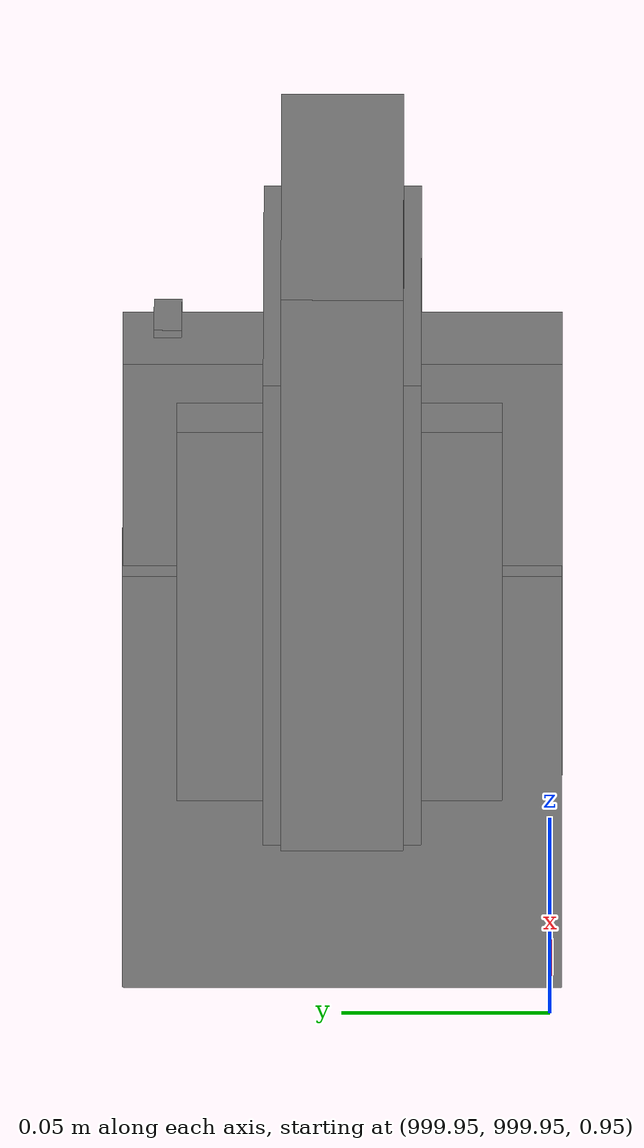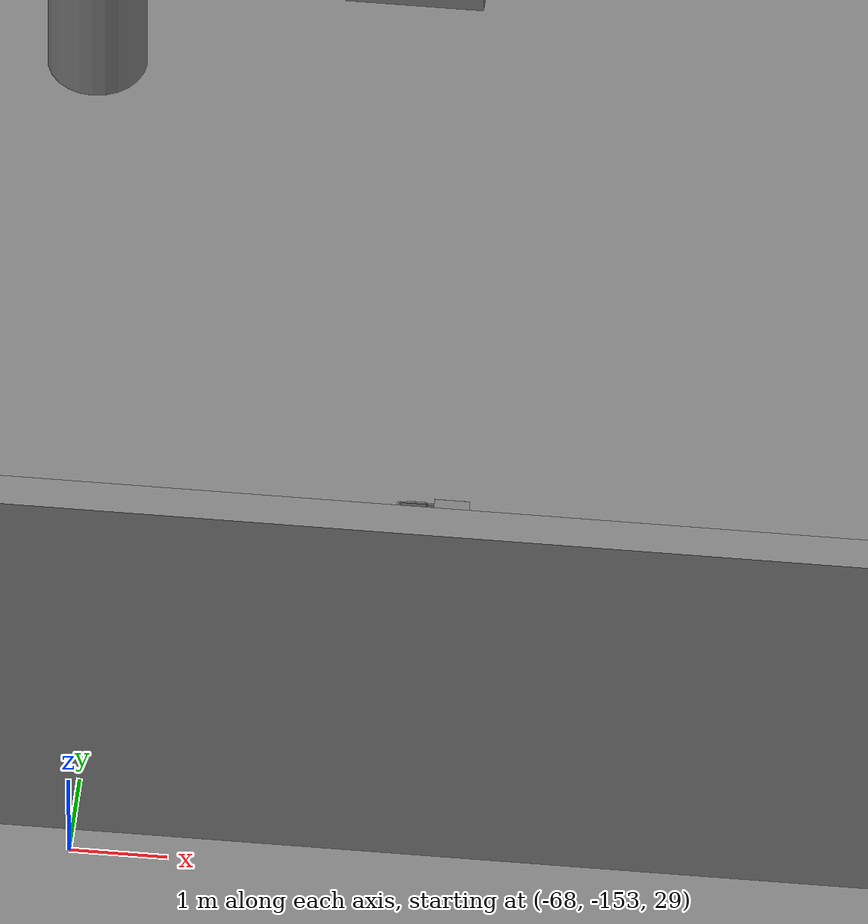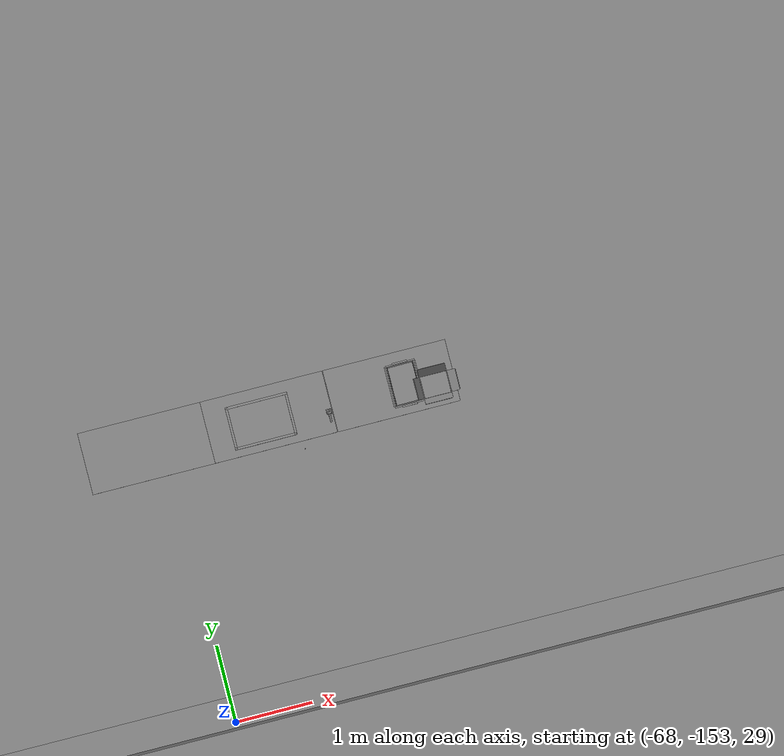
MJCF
<mujoco>
    <option gravity="0.000000000 0.000000000 -9.810000420" timestep="0.0049999999" integrator="implicitfast" density="1.225" viscosity="1.8000001e-05" noslip_iterations="10" iterations="100" sdf_iterations="50">
        <flag multiccd="disable"/>
    </option>
    <size memory="1000M"/>
    <compiler coordinate="local"/>
    <worldbody>
        <light cutoff="30" pos="0 1 1" dir="0 -1 -2"/>
        <light cutoff="30" pos="0 -1 1" dir="0 1 -2"/>
        <body pos="1000.000000000 1000.000000000 1.000000000" euler="0.000000000 0.000000000 180.000000000" name="openloong_gripper_2f85_fix_base_usda_cpu_fan">
            <geom contype="1" conaffinity="1" density="1000" type="box" material="" rgba="0.500000000 0.500000000 0.500000000 1.000000000" solimp="0.899999976 0.949999988 0.001000000" friction="1.000000000 0.005000000 0.000100000" solref="0.020000000 1.000000000" margin="0" condim="3" group="0" pos="0.000000000 0.000000000 0.070034981" quat="0.000000000 0.000000000 0.000000000 1.000000000" size="0.070700005 0.014699999 0.070700005" name="openloong_gripper_2f85_fix_base_usda_geom_46F16A02_790B_4617_8732_51EB69466A20"/>
            <freejoint name="openloong_gripper_2f85_fix_base_usda_cpu_fan_joint"/>
            <site size="0.005000000 0.005000000 0.005000000" rgba="0.500000000 0.500000000 0.500000000 1.000000000" pos="0.000000000 0.000000000 0.000000000" quat="0.999961913 0.008726535 0.000000000 0.000000000" group="0" type="sphere" name="openloong_gripper_2f85_fix_base_usda_cpu_fancsite"/>
        </body>
        <body pos="1000.000000000 1000.000000000 1.000000000" euler="0.000000000 0.000000000 180.000000000" name="openloong_gripper_2f85_fix_base_usda_battery_01">
            <geom contype="1" conaffinity="1" density="1000" type="box" material="" rgba="0.500000000 0.500000000 0.500000000 1.000000000" solimp="0.899999976 0.949999988 0.001000000" friction="1.000000000 0.005000000 0.000100000" solref="0.020000000 1.000000000" margin="0" condim="3" group="0" pos="-0.011123657 -0.041940309 0.101691343" quat="1.000000000 0.000000000 0.000000000 0.000000000" size="0.010800000 0.003375000 0.004725000" name="openloong_gripper_2f85_fix_base_usda_geom_78C2CDCE_D7A9_4638_B129_09AFAB42299B"/>
            <geom contype="1" conaffinity="1" density="1000" type="box" material="" rgba="0.500000000 0.500000000 0.500000000 1.000000000" solimp="0.899999976 0.949999988 0.001000000" friction="1.000000000 0.005000000 0.000100000" solref="0.020000000 1.000000000" margin="0" condim="3" group="0" pos="-0.010876465 -0.044247437 0.047066893" quat="0.998702705 -0.050920475 0.000000000 0.000000000" size="0.009450001 0.002700000 0.024975000" name="openloong_gripper_2f85_fix_base_usda_geom_B6E8D4D5_1B17_4EEB_9EA6_D10736B62CB9"/>
            <geom contype="1" conaffinity="1" density="1000" type="box" material="" rgba="0.500000000 0.500000000 0.500000000 1.000000000" solimp="0.899999976 0.949999988 0.001000000" friction="1.000000000 0.005000000 0.000100000" solref="0.020000000 1.000000000" margin="0" condim="3" group="0" pos="-0.001235962 -0.000659180 0.047381196" quat="1.000000000 0.000000000 0.000000000 0.000000000" size="0.039420001 0.039150000 0.047250003" name="openloong_gripper_2f85_fix_base_usda_geom_CDE79191_CDB1_44BB_9648_AFFBDFE5D440"/>
            <geom contype="1" conaffinity="1" density="1000" type="box" material="" rgba="0.500000000 0.500000000 0.500000000 1.000000000" solimp="0.899999976 0.949999988 0.001000000" friction="1.000000000 0.005000000 0.000100000" solref="0.020000000 1.000000000" margin="0" condim="3" group="0" pos="-0.010876465 -0.039138794 0.009851727" quat="1.000000000 0.000000000 0.000000000 0.000000000" size="0.009450001 0.010800000 0.013500000" name="openloong_gripper_2f85_fix_base_usda_geom_D5862AB2_ECDE_4493_A196_4DD61AEFFC93"/>
            <geom contype="1" conaffinity="1" density="1000" type="box" material="" rgba="0.500000000 0.500000000 0.500000000 1.000000000" solimp="0.899999976 0.949999988 0.001000000" friction="1.000000000 0.005000000 0.000100000" solref="0.020000000 1.000000000" margin="0" condim="3" group="0" pos="-0.010876465 -0.041528322 0.071508206" quat="1.000000000 0.000000000 0.000000000 0.000000000" size="0.009450001 0.002700000 0.027000001" name="openloong_gripper_2f85_fix_base_usda_geom_E43EE97C_13AC_4E3F_84DB_B01A03D11946"/>
            <freejoint name="openloong_gripper_2f85_fix_base_usda_battery_01_joint"/>
            <site size="0.005000000 0.005000000 0.005000000" rgba="0.500000000 0.500000000 0.500000000 1.000000000" pos="0.000000000 0.000000000 0.000000000" quat="0.999961913 0.008726500 0.000000000 0.000000000" group="0" type="sphere" name="openloong_gripper_2f85_fix_base_usda_battery_01site"/>
        </body>
        <body pos="1000.000000000 1000.000000000 1.000000000" euler="0.000000000 0.000000000 180.000000000" name="openloong_gripper_2f85_fix_base_usda_wifi_box">
            <geom contype="1" conaffinity="1" density="1000" type="box" material="" rgba="0.500000000 0.500000000 0.500000000 1.000000000" solimp="0.899999976 0.949999988 0.001000000" friction="1.000000000 0.005000000 0.000100000" solref="0.020000000 1.000000000" margin="0" condim="3" group="0" pos="0.000000000 0.000000000 0.058978677" quat="0.000000000 0.000000047 0.000000000 1.000000000" size="0.068499997 0.018999999 0.059000000" name="openloong_gripper_2f85_fix_base_usda_geom_7BCB9F06_7F92_42D1_B326_842400101624"/>
            <freejoint name="openloong_gripper_2f85_fix_base_usda_wifi_box_joint"/>
            <site size="0.005000000 0.005000000 0.005000000" rgba="0.500000000 0.500000000 0.500000000 1.000000000" pos="0.000000000 0.000000000 0.000000000" quat="0.999961913 0.008726500 0.000000000 0.000000000" group="0" type="sphere" name="openloong_gripper_2f85_fix_base_usda_wifi_boxsite"/>
        </body>
        <body pos="-66.119949341 -149.071060181 31.165760040" euler="98.650787354 -3.070183277 -162.530136108" mocap="true" name="spotlight6_SpotLight"/>
        <body pos="1000.000000000 1000.000000000 1.000000000" euler="0.000011953 0.000005123 -179.999984741" name="openloong_gripper_2f85_fix_base_usda_intel_box">
            <geom contype="1" conaffinity="1" density="1000" type="box" material="" rgba="0.500000000 0.500000000 0.500000000 1.000000000" solimp="0.899999976 0.949999988 0.001000000" friction="1.000000000 0.005000000 0.000100000" solref="0.020000000 1.000000000" margin="0" condim="3" group="0" pos="0.000000000 -0.000067139 0.000082284" quat="0.707106709 0.000000225 0.000000253 0.707106650" size="0.052800003 0.025300000 0.052800003" name="openloong_gripper_2f85_fix_base_usda_geom_81CFE785_DCF8_4AC2_864B_B5F4391A436D"/>
            <freejoint name="openloong_gripper_2f85_fix_base_usda_intel_box_joint"/>
            <site size="0.005000000 0.005000000 0.005000000" rgba="0.500000000 0.500000000 0.500000000 1.000000000" pos="0.000000000 0.000000000 0.000000000" quat="0.999961913 0.008726500 0.000000000 0.000000000" group="0" type="sphere" name="openloong_gripper_2f85_fix_base_usda_intel_boxsite"/>
        </body>
        <body pos="1000.000000000 999.999938965 1.000000000" euler="0.000000000 0.000000000 180.000000000" name="openloong_gripper_2f85_fix_base_usda_intelcore_i5">
            <geom contype="1" conaffinity="1" density="1000" type="box" material="" rgba="0.500000000 0.500000000 0.500000000 1.000000000" solimp="0.899999976 0.949999988 0.001000000" friction="1.000000000 0.005000000 0.000100000" solref="0.020000000 1.000000000" margin="0" condim="3" group="0" pos="0.000000000 0.000000000 0.051722717" quat="0.707106709 0.000000000 0.000000000 -0.707106769" size="0.052800000 0.018080002 0.052800000" name="openloong_gripper_2f85_fix_base_usda_geom_E2FE692B_6D5D_4534_9680_1B83C79AADF4"/>
            <freejoint name="openloong_gripper_2f85_fix_base_usda_intelcore_i5_joint"/>
            <site size="0.005000000 0.005000000 0.005000000" rgba="0.500000000 0.500000000 0.500000000 1.000000000" pos="0.000000000 0.000000000 0.000000000" quat="0.999961913 0.008726534 0.000000000 0.000000000" group="0" type="sphere" name="openloong_gripper_2f85_fix_base_usda_intelcore_i5site"/>
        </body>
        <body pos="-66.033378601 -149.703948975 31.165111542" euler="127.478202820 4.069211006 -3.403380156" mocap="true" name="spotlight1_SpotLight"/>
        <body pos="-66.283500671 -149.257476807 31.164123535" euler="-100.206535339 45.797126770 -10.070066452" mocap="true" name="spotlight4_SpotLight"/>
        <body pos="-64.866622925 -149.383972168 30.183746338" euler="89.999984741 89.999946594 0.000000000" name="openloong_gripper_2f85_fix_base_usda_bluebox_01">
            <geom contype="1" conaffinity="1" density="1000" type="box" material="" rgba="0.500000000 0.500000000 0.500000000 1.000000000" solimp="0.899999976 0.949999988 0.001000000" friction="1.000000000 0.005000000 0.000100000" solref="0.020000000 1.000000000" margin="0" condim="3" group="0" pos="0.276580811 0.187225342 0.000068665" quat="0.707106948 0.000077471 0.707106352 0.000077486" size="0.100000001 0.057999998 0.010000000" name="openloong_gripper_2f85_fix_base_usda_geom_C1B630E4_E855_4354_8FC7_C40E94812361"/>
            <geom contype="1" conaffinity="1" density="1000" type="box" material="" rgba="0.500000000 0.500000000 0.500000000 1.000000000" solimp="0.899999976 0.949999988 0.001000000" friction="1.000000000 0.005000000 0.000100000" solref="0.020000000 1.000000000" margin="0" condim="3" group="0" pos="0.000000000 0.002883911 0.000000000" quat="0.999999881 0.000000000 0.000000000 0.000000000" size="0.254000008 0.003000000 0.172000006" name="openloong_gripper_2f85_fix_base_usda_geom_E3DEA63D_C669_42DF_9D9B_4C1C76CB8205"/>
            <geom contype="1" conaffinity="1" density="1000" type="box" material="" rgba="0.500000000 0.500000000 0.500000000 1.000000000" solimp="0.899999976 0.949999988 0.001000000" friction="1.000000000 0.005000000 0.000100000" solref="0.020000000 1.000000000" margin="0" condim="3" group="0" pos="0.000000000 0.124874115 0.173484802" quat="0.999796331 0.020176515 -0.000000015 0.000000030" size="0.259999990 0.119999997 0.007000000" name="openloong_gripper_2f85_fix_base_usda_geom_793F9C70_D91A_463E_935A_44BA3D361959"/>
            <geom contype="1" conaffinity="1" density="1000" type="box" material="" rgba="0.500000000 0.500000000 0.500000000 1.000000000" solimp="0.899999976 0.949999988 0.001000000" friction="1.000000000 0.005000000 0.000100000" solref="0.020000000 1.000000000" margin="0" condim="3" group="0" pos="0.000000000 0.124874115 -0.173469543" quat="0.999796331 -0.020176545 -0.000000015 0.000000000" size="0.259999990 0.119999997 0.007000000" name="openloong_gripper_2f85_fix_base_usda_geom_AE229A89_CF01_4046_929F_F618408FA0E3"/>
            <geom contype="1" conaffinity="1" density="1000" type="box" material="" rgba="0.500000000 0.500000000 0.500000000 1.000000000" solimp="0.899999976 0.949999988 0.001000000" friction="1.000000000 0.005000000 0.000100000" solref="0.020000000 1.000000000" margin="0" condim="3" group="0" pos="0.000000000 0.214008331 0.188980103" quat="0.999912977 0.013176724 0.000000015 0.000000000" size="0.259999990 0.029999999 0.012500000" name="openloong_gripper_2f85_fix_base_usda_geom_EB4BD1AF_2915_405A_9453_489405F734B1"/>
            <geom contype="1" conaffinity="1" density="1000" type="box" material="" rgba="0.500000000 0.500000000 0.500000000 1.000000000" solimp="0.899999976 0.949999988 0.001000000" friction="1.000000000 0.005000000 0.000100000" solref="0.020000000 1.000000000" margin="0" condim="3" group="0" pos="-0.258361816 0.125289917 0.001876831" quat="0.702796936 -0.020792112 0.710783124 0.020769298" size="0.189999998 0.119999997 0.009000000" name="openloong_gripper_2f85_fix_base_usda_geom_944B0005_9EAC_45B0_9915_B2D13FF577B6"/>
            <geom contype="1" conaffinity="1" density="1000" type="box" material="" rgba="0.500000000 0.500000000 0.500000000 1.000000000" solimp="0.899999976 0.949999988 0.001000000" friction="1.000000000 0.005000000 0.000100000" solref="0.020000000 1.000000000" margin="0" condim="3" group="0" pos="0.000000000 0.214008331 -0.188980103" quat="0.999912977 -0.013176769 0.000000030 0.000000015" size="0.259999990 0.029999999 0.012500000" name="openloong_gripper_2f85_fix_base_usda_geom_E1D427FF_CDB1_451B_96B7_F6F2919A6055"/>
            <geom contype="1" conaffinity="1" density="1000" type="box" material="" rgba="0.500000000 0.500000000 0.500000000 1.000000000" solimp="0.899999976 0.949999988 0.001000000" friction="1.000000000 0.005000000 0.000100000" solref="0.020000000 1.000000000" margin="0" condim="3" group="0" pos="-0.276611328 0.187225342 0.000068665" quat="0.707106650 0.000077441 0.707106709 0.000077456" size="0.100000001 0.057999998 0.010000000" name="openloong_gripper_2f85_fix_base_usda_geom_EF0DC25D_1F72_419C_B880_FCDA3204944D"/>
            <geom contype="1" conaffinity="1" density="1000" type="box" material="" rgba="0.500000000 0.500000000 0.500000000 1.000000000" solimp="0.899999976 0.949999988 0.001000000" friction="1.000000000 0.005000000 0.000100000" solref="0.020000000 1.000000000" margin="0" condim="3" group="0" pos="0.258331299 0.125289917 0.001876831" quat="0.702851415 0.018856421 0.710823774 -0.019329369" size="0.189999998 0.119999997 0.009000000" name="openloong_gripper_2f85_fix_base_usda_geom_28BF832D_C187_4FF1_B7D7_5FC8F9941A5B"/>
            <freejoint name="openloong_gripper_2f85_fix_base_usda_bluebox_01_joint"/>
            <site size="0.005000000 0.005000000 0.005000000" rgba="0.500000000 0.500000000 0.500000000 1.000000000" pos="0.000000000 0.000000000 0.000000000" quat="0.999961913 0.008726534 0.000000000 0.000000000" group="0" type="sphere" name="openloong_gripper_2f85_fix_base_usda_bluebox_01site"/>
        </body>
        <body pos="-64.496299744 -149.491867065 30.235729218" euler="0.000000000 0.000000000 89.999946594" name="openloong_gripper_2f85_fix_base_usda_cardboardbox_01">
            <geom contype="1" conaffinity="1" density="1000" type="box" material="" rgba="0.500000000 0.500000000 0.500000000 1.000000000" solimp="0.899999976 0.949999988 0.001000000" friction="1.000000000 0.005000000 0.000100000" solref="0.020000000 1.000000000" margin="0" condim="3" group="0" pos="-0.003166199 -0.004086494 0.005052090" quat="1.000000000 0.000000000 0.000000000 0.000000000" size="0.142499998 0.177500010 0.005000000" name="openloong_gripper_2f85_fix_base_usda_geom_A01BB2CA_15C1_4DAD_B6CF_1F5CC37D88DC"/>
            <geom contype="1" conaffinity="1" density="1000" type="box" material="" rgba="0.500000000 0.500000000 0.500000000 1.000000000" solimp="0.899999976 0.949999988 0.001000000" friction="1.000000000 0.005000000 0.000100000" solref="0.020000000 1.000000000" margin="0" condim="3" group="0" pos="-0.003166199 0.170316696 0.150570869" quat="1.000000000 0.000000000 0.000000000 0.000000000" size="0.142499998 0.005000000 0.149999991" name="openloong_gripper_2f85_fix_base_usda_geom_AD9698F7_7CE2_4DBE_8BD4_B3D8966395E1"/>
            <geom contype="1" conaffinity="1" density="1000" type="box" material="" rgba="0.500000000 0.500000000 0.500000000 1.000000000" solimp="0.899999976 0.949999988 0.001000000" friction="1.000000000 0.005000000 0.000100000" solref="0.020000000 1.000000000" margin="0" condim="3" group="0" pos="-0.147399902 -0.005307198 0.150570869" quat="1.000000000 0.000000000 0.000000000 0.000000000" size="0.005000000 0.177500010 0.149999991" name="openloong_gripper_2f85_fix_base_usda_geom_134A4B5F_17FF_4E44_A25A_34B461500ED1"/>
            <geom contype="1" conaffinity="1" density="1000" type="box" material="" rgba="0.500000000 0.500000000 0.500000000 1.000000000" solimp="0.899999976 0.949999988 0.001000000" friction="1.000000000 0.005000000 0.000100000" solref="0.020000000 1.000000000" margin="0" condim="3" group="0" pos="0.140275955 -0.005307198 0.150570869" quat="1.000000000 0.000000000 0.000000000 0.000000000" size="0.005000000 0.177500010 0.149999991" name="openloong_gripper_2f85_fix_base_usda_geom_BC592E68_478B_4EE2_8341_3C250B5CC22A"/>
            <geom contype="1" conaffinity="1" density="1000" type="box" material="" rgba="0.500000000 0.500000000 0.500000000 1.000000000" solimp="0.899999976 0.949999988 0.001000000" friction="1.000000000 0.005000000 0.000100000" solref="0.020000000 1.000000000" margin="0" condim="3" group="0" pos="-0.003166199 -0.181550980 0.150570869" quat="1.000000000 0.000000000 0.000000000 0.000000000" size="0.142499998 0.005000000 0.149999991" name="openloong_gripper_2f85_fix_base_usda_geom_26B77107_9A28_4DC2_A305_86E612DA3A75"/>
            <freejoint name="openloong_gripper_2f85_fix_base_usda_cardboardbox_01_joint"/>
            <site size="0.005000000 0.005000000 0.005000000" rgba="0.500000000 0.500000000 0.500000000 1.000000000" pos="0.000000000 0.000000000 0.000000000" quat="0.999961913 0.008726535 0.000000000 0.000000000" group="0" type="sphere" name="openloong_gripper_2f85_fix_base_usda_site_2DA27CE5_3B5A_445A_A0DD_9DB7136BD3EE"/>
            <body pos="0.139160156 -0.004048347 0.301930904" euler="-179.999954224 49.383502960 179.999954224" name="openloong_gripper_2f85_fix_base_usda_A1_006">
                <geom contype="1" conaffinity="1" density="1000" type="box" material="" rgba="0.500000000 0.500000000 0.500000000 1.000000000" solimp="0.899999976 0.949999988 0.001000000" friction="1.000000000 0.005000000 0.000100000" solref="0.020000000 1.000000000" margin="0" condim="3" group="0" pos="-0.071587563 0.000009537 0.001745224" quat="0.999999881 0.000000000 0.000000000 0.000000000" size="0.071249999 0.179999992 0.002500000" name="openloong_gripper_2f85_fix_base_usda_geom_C87E75E2_F577_4D7D_B82C_568104B11006"/>
                <joint armature="0" stiffness="0.07" damping="0.0099999998" axis="0.000000 1.000000 0.000000" type="hinge" name="openloong_gripper_2f85_fix_base_usda_A1_006"/>
            </body>
            <body pos="-0.145902634 -0.004086494 0.301938057" euler="-180.000000000 -60.000011444 -180.000000000" name="openloong_gripper_2f85_fix_base_usda_A2_006">
                <geom contype="1" conaffinity="1" density="1000" type="box" material="" rgba="0.500000000 0.500000000 0.500000000 1.000000000" solimp="0.899999976 0.949999988 0.001000000" friction="1.000000000 0.005000000 0.000100000" solref="0.020000000 1.000000000" margin="0" condim="3" group="0" pos="0.071268082 0.000009537 0.002717972" quat="0.000002921 0.000000000 -0.000000030 0.999999881" size="0.071249999 0.179999992 0.002500000" name="openloong_gripper_2f85_fix_base_usda_geom_813D0454_E20D_42E3_BFB8_F5AE19938CFA"/>
                <joint armature="0" stiffness="0.07" damping="0.0099999998" axis="0.000000 1.000000 0.000000" type="hinge" name="openloong_gripper_2f85_fix_base_usda_A2_006"/>
            </body>
            <body pos="-0.003385544 0.175991058 0.301930904" euler="-125.858116150 -0.000004561 0.000002331" name="openloong_gripper_2f85_fix_base_usda_B2_006">
                <geom contype="1" conaffinity="1" density="1000" type="box" material="" rgba="0.500000000 0.500000000 0.500000000 1.000000000" solimp="0.899999976 0.949999988 0.001000000" friction="1.000000000 0.005000000 0.000100000" solref="0.020000000 1.000000000" margin="0" condim="3" group="0" pos="0.000009537 -0.070939064 -0.002470016" quat="0.999614120 0.027776197 -0.000000015 0.000000030" size="0.137500003 0.064999998 0.005000000" name="openloong_gripper_2f85_fix_base_usda_geom_5DF64FEB_4CCC_4165_8EB0_FD181BB4339D"/>
                <joint armature="0" stiffness="0.07" damping="0.0099999998" axis="1.000000 0.000000 0.000000" type="hinge" name="openloong_gripper_2f85_fix_base_usda_B2_006"/>
            </body>
            <body pos="-0.003385544 -0.184140205 0.301938057" euler="147.805557251 0.000000000 0.000000000" name="openloong_gripper_2f85_fix_base_usda_B1_006">
                <geom contype="1" conaffinity="1" density="1000" type="box" material="" rgba="0.500000000 0.500000000 0.500000000 1.000000000" solimp="0.899999976 0.949999988 0.001000000" friction="1.000000000 0.005000000 0.000100000" solref="0.020000000 1.000000000" margin="0" condim="3" group="0" pos="-0.000028610 0.070202351 -0.002703667" quat="0.999614179 -0.027776167 0.000000000 0.000000000" size="0.137500003 0.064999998 0.005000000" name="openloong_gripper_2f85_fix_base_usda_geom_6676FC2E_383D_4B36_9FC1_A435EDEE1FBE"/>
                <joint armature="0" stiffness="0.07" damping="0.0099999998" axis="1.000000 0.000000 0.000000" type="hinge" name="openloong_gripper_2f85_fix_base_usda_B1_006"/>
            </body>
        </body>
        <body pos="-65.882858276 -149.481979370 30.229999542" euler="-64.487716675 0.000000000 0.000000000" name="openloong_gripper_2f85_fix_base_usda_Barcode">
            <geom contype="1" conaffinity="1" density="1000" type="box" material="" rgba="0.500000000 0.500000000 0.500000000 1.000000000" solimp="0.899999976 0.949999988 0.001000000" friction="1.000000000 0.005000000 0.000100000" solref="0.020000000 1.000000000" margin="0" condim="3" group="0" pos="0.000000000 0.013038635 0.001419067" quat="0.000000000 0.000000000 0.000000000 1.000000119" size="0.034000002 0.010000000 0.017999999" name="openloong_gripper_2f85_fix_base_usda_geom_2A7E3287_3A51_4437_AAE0_1A24C539AA4A"/>
            <geom contype="1" conaffinity="1" density="1000" type="box" material="" rgba="0.500000000 0.500000000 0.500000000 1.000000000" solimp="0.899999976 0.949999988 0.001000000" friction="1.000000000 0.005000000 0.000100000" solref="0.020000000 1.000000000" margin="0" condim="3" group="0" pos="0.000000000 -0.035301208 -0.007095337" quat="0.000000000 0.000000000 -0.043619365 0.999048233" size="0.028999999 0.010000000 0.020000000" name="openloong_gripper_2f85_fix_base_usda_geom_F30D6972_12D9_4779_BF58_856BB5E21A31"/>
            <geom contype="1" conaffinity="1" density="1000" type="box" material="" rgba="0.500000000 0.500000000 0.500000000 1.000000000" solimp="0.899999976 0.949999988 0.001000000" friction="1.000000000 0.005000000 0.000100000" solref="0.020000000 1.000000000" margin="0" condim="3" group="0" pos="0.000000000 -0.043411255 -0.011749268" quat="0.922262907 0.386563420 0.000000000 0.000000000" size="0.026000001 0.010000000 0.020000000" name="openloong_gripper_2f85_fix_base_usda_geom_FEF14237_9C1F_4957_94E8_D57105D3E882"/>
            <geom contype="1" conaffinity="1" density="1000" type="box" material="" rgba="0.500000000 0.500000000 0.500000000 1.000000000" solimp="0.899999976 0.949999988 0.001000000" friction="1.000000000 0.005000000 0.000100000" solref="0.020000000 1.000000000" margin="0" condim="3" group="0" pos="0.000000000 -0.016967773 -0.031860352" quat="0.000000000 0.000000000 0.000000000 1.000000119" size="0.008000000 0.010000000 0.013000000" name="openloong_gripper_2f85_fix_base_usda_geom_B72A6E0C_CBB1_4A81_B25F_C78F2656AF3B"/>
            <geom contype="1" conaffinity="1" density="1000" type="box" material="" rgba="0.500000000 0.500000000 0.500000000 1.000000000" solimp="0.899999976 0.949999988 0.001000000" friction="1.000000000 0.005000000 0.000100000" solref="0.020000000 1.000000000" margin="0" condim="3" group="0" pos="0.000000000 -0.001869202 0.000312805" quat="0.953716993 0.300705761 0.000000000 0.000000000" size="0.032000002 0.010000000 0.018999999" name="openloong_gripper_2f85_fix_base_usda_geom_881502D2_52F5_4444_A09D_EFADEF64321B"/>
            <geom contype="1" conaffinity="1" density="1000" type="box" material="" rgba="0.500000000 0.500000000 0.500000000 1.000000000" solimp="0.899999976 0.949999988 0.001000000" friction="1.000000000 0.005000000 0.000100000" solref="0.020000000 1.000000000" margin="0" condim="3" group="0" pos="0.000000000 -0.019531250 -0.003173828" quat="0.953716993 0.300705761 0.000000000 0.000000000" size="0.030999999 0.010000000 0.020000000" name="openloong_gripper_2f85_fix_base_usda_geom_6A1BFA53_ED15_41CE_9954_A5C4762EAF4A"/>
            <geom contype="1" conaffinity="1" density="1000" type="box" material="" rgba="0.500000000 0.500000000 0.500000000 1.000000000" solimp="0.899999976 0.949999988 0.001000000" friction="1.000000000 0.005000000 0.000100000" solref="0.020000000 1.000000000" margin="0" condim="3" group="0" pos="0.000000000 -0.035301208 -0.007095337" quat="0.953716993 0.300705761 0.000000000 0.000000000" size="0.028999999 0.010000000 0.020000000" name="openloong_gripper_2f85_fix_base_usda_geom_84F1E09D_CB6A_4E4F_95B0_D0F87B8973E2"/>
            <geom contype="1" conaffinity="1" density="1000" type="box" material="" rgba="0.500000000 0.500000000 0.500000000 1.000000000" solimp="0.899999976 0.949999988 0.001000000" friction="1.000000000 0.005000000 0.000100000" solref="0.020000000 1.000000000" margin="0" condim="3" group="0" pos="0.000000000 -0.042617798 -0.071121216" quat="0.000000000 0.000000000 0.000000000 1.000000119" size="0.013000000 0.021000000 0.059999999" name="openloong_gripper_2f85_fix_base_usda_geom_3FCD18E8_DAED_4E42_AEF8_4B3C90AD93FD"/>
            <freejoint name="openloong_gripper_2f85_fix_base_usda_Barcode_joint"/>
            <site size="0.005000000 0.005000000 0.005000000" rgba="0.500000000 0.500000000 0.500000000 1.000000000" pos="0.000000000 0.000000000 0.000000000" quat="1.000000000 0.000000000 0.000000000 0.000000000" group="0" type="sphere" name="openloong_gripper_2f85_fix_base_usda_Barcode_site"/>
        </body>
        <body pos="-66.745018005 -149.392349243 30.184000015" euler="0.000000000 0.000000000 89.999946594" name="[22331047805524]_Basket_01">
            <geom contype="1" conaffinity="1" density="1000" type="box" material="" rgba="0.500000000 0.500000000 0.500000000 1.000000000" solimp="0.899999976 0.949999988 0.001000000" friction="1.000000000 0.005000000 0.000100000" solref="0.020000000 1.000000000" margin="0" condim="3" group="0" pos="-0.052425385 0.389207840 0.089787483" quat="0.707107008 0.000000000 0.000000000 0.707106411" size="0.014249999 0.014249999 0.059999999" name="[22331047805524]_geom_29C9D26B_30E9_4468_A53B_59C3E1999F2F"/>
            <geom contype="1" conaffinity="1" density="1000" type="box" material="" rgba="0.500000000 0.500000000 0.500000000 1.000000000" solimp="0.899999976 0.949999988 0.001000000" friction="1.000000000 0.005000000 0.000100000" solref="0.020000000 1.000000000" margin="0" condim="3" group="0" pos="0.264015198 -0.133043289 0.089787483" quat="0.707107008 0.000000000 0.000000000 0.707106411" size="0.014249999 0.014249999 0.059999999" name="[22331047805524]_geom_E5F24A3F_C6F6_432E_BA51_AD8B52B99EA2"/>
            <geom contype="1" conaffinity="1" density="1000" type="box" material="" rgba="0.500000000 0.500000000 0.500000000 1.000000000" solimp="0.899999976 0.949999988 0.001000000" friction="1.000000000 0.005000000 0.000100000" solref="0.020000000 1.000000000" margin="0" condim="3" group="0" pos="-0.264015198 -0.265548706 0.089793205" quat="0.707107008 0.000000000 0.000000000 0.707106411" size="0.014249999 0.014249999 0.059999999" name="[22331047805524]_geom_7EB6B986_B490_4D05_8837_DE60AF3F3BB3"/>
            <geom contype="1" conaffinity="1" density="1000" type="box" material="" rgba="0.500000000 0.500000000 0.500000000 1.000000000" solimp="0.899999976 0.949999988 0.001000000" friction="1.000000000 0.005000000 0.000100000" solref="0.020000000 1.000000000" margin="0" condim="3" group="0" pos="-0.160263062 -0.389322281 0.089793205" quat="0.707107008 0.000000000 0.000000000 0.707106411" size="0.014249999 0.014249999 0.059999999" name="[22331047805524]_geom_0A1CBDE0_9C1D_4593_9F91_827F8DB5F4D9"/>
            <geom contype="1" conaffinity="1" density="1000" type="box" material="" rgba="0.500000000 0.500000000 0.500000000 1.000000000" solimp="0.899999976 0.949999988 0.001000000" friction="1.000000000 0.005000000 0.000100000" solref="0.020000000 1.000000000" margin="0" condim="3" group="0" pos="0.162265778 -0.389322281 0.089787483" quat="0.707107008 0.000000000 0.000000000 0.707106411" size="0.014249999 0.014249999 0.059999999" name="[22331047805524]_geom_BE84EB0C_E8D8_4AD2_9556_090A789FB063"/>
            <geom contype="1" conaffinity="1" density="1000" type="box" material="" rgba="0.500000000 0.500000000 0.500000000 1.000000000" solimp="0.899999976 0.949999988 0.001000000" friction="1.000000000 0.005000000 0.000100000" solref="0.020000000 1.000000000" margin="0" condim="3" group="0" pos="0.264015198 0.389207840 0.089787483" quat="0.707107008 0.000000000 0.000000000 0.707106411" size="0.014249999 0.014249999 0.059999999" name="[22331047805524]_geom_64D78A3D_0F01_41CC_9E5F_D66F328B5906"/>
            <geom contype="1" conaffinity="1" density="1000" type="box" material="" rgba="0.500000000 0.500000000 0.500000000 1.000000000" solimp="0.899999976 0.949999988 0.001000000" friction="1.000000000 0.005000000 0.000100000" solref="0.020000000 1.000000000" margin="0" condim="3" group="0" pos="-0.264015198 -0.133043289 0.089793205" quat="0.707107008 0.000000000 0.000000000 0.707106411" size="0.014249999 0.014249999 0.059999999" name="[22331047805524]_geom_21CC9F74_0522_46C4_B874_A0823EAC027A"/>
            <geom contype="1" conaffinity="1" density="1000" type="box" material="" rgba="0.500000000 0.500000000 0.500000000 1.000000000" solimp="0.899999976 0.949999988 0.001000000" friction="1.000000000 0.005000000 0.000100000" solref="0.020000000 1.000000000" margin="0" condim="3" group="0" pos="-0.264026642 0.269256592 0.089793205" quat="0.707107008 0.000000000 0.000000000 0.707106411" size="0.014249999 0.014249999 0.059999999" name="[22331047805524]_geom_54B33808_A189_4365_AC40_EBB74752CBAE"/>
            <geom contype="1" conaffinity="1" density="1000" type="box" material="" rgba="0.500000000 0.500000000 0.500000000 1.000000000" solimp="0.899999976 0.949999988 0.001000000" friction="1.000000000 0.005000000 0.000100000" solref="0.020000000 1.000000000" margin="0" condim="3" group="0" pos="0.054462433 0.389207840 0.089787483" quat="0.707107008 0.000000000 0.000000000 0.707106411" size="0.014249999 0.014249999 0.059999999" name="[22331047805524]_geom_2235520B_F870_4926_ACD6_1689DE2F90B6"/>
            <geom contype="1" conaffinity="1" density="1000" type="box" material="" rgba="0.500000000 0.500000000 0.500000000 1.000000000" solimp="0.899999976 0.949999988 0.001000000" friction="1.000000000 0.005000000 0.000100000" solref="0.020000000 1.000000000" margin="0" condim="3" group="0" pos="0.054462433 -0.389322281 0.089787483" quat="0.707107008 0.000000000 0.000000000 0.707106411" size="0.014249999 0.014249999 0.059999999" name="[22331047805524]_geom_E8B386F4_82A7_4C24_B6BF_845EE0BB41C0"/>
            <geom contype="1" conaffinity="1" density="1000" type="box" material="" rgba="0.500000000 0.500000000 0.500000000 1.000000000" solimp="0.899999976 0.949999988 0.001000000" friction="1.000000000 0.005000000 0.000100000" solref="0.020000000 1.000000000" margin="0" condim="3" group="0" pos="0.264015198 0.269256592 0.089793205" quat="0.707107008 0.000000000 0.000000000 0.707106411" size="0.014249999 0.014249999 0.059999999" name="[22331047805524]_geom_B5C7C6C3_3AFA_4CA5_B74C_ED20A28A5AA1"/>
            <geom contype="1" conaffinity="1" density="1000" type="box" material="" rgba="0.500000000 0.500000000 0.500000000 1.000000000" solimp="0.899999976 0.949999988 0.001000000" friction="1.000000000 0.005000000 0.000100000" solref="0.020000000 1.000000000" margin="0" condim="3" group="0" pos="0.264015198 -0.389322281 0.089787483" quat="0.707107008 0.000000000 0.000000000 0.707106411" size="0.014249999 0.014249999 0.059999999" name="[22331047805524]_geom_DD9BB562_8FEA_43D7_934F_8936FC432354"/>
            <geom contype="1" conaffinity="1" density="1000" type="box" material="" rgba="0.500000000 0.500000000 0.500000000 1.000000000" solimp="0.899999976 0.949999988 0.001000000" friction="1.000000000 0.005000000 0.000100000" solref="0.020000000 1.000000000" margin="0" condim="3" group="0" pos="0.000000000 0.000000000 0.015998840" quat="0.707107008 0.000000000 0.000000000 0.707106411" size="0.403499991 0.279000014 0.015750000" name="[22331047805524]_geom_AE02880B_D9D6_475B_BA97_EF54D5742214"/>
            <geom contype="1" conaffinity="1" density="1000" type="box" material="" rgba="0.500000000 0.500000000 0.500000000 1.000000000" solimp="0.899999976 0.949999988 0.001000000" friction="1.000000000 0.005000000 0.000100000" solref="0.020000000 1.000000000" margin="0" condim="3" group="0" pos="0.000000000 -0.389476776 0.163619041" quat="0.707107008 0.000000000 0.000000000 0.707106411" size="0.015000000 0.277500004 0.015750000" name="[22331047805524]_geom_239F6F73_1504_479A_98F7_15D960BEC6BC"/>
            <geom contype="1" conaffinity="1" density="1000" type="box" material="" rgba="0.500000000 0.500000000 0.500000000 1.000000000" solimp="0.899999976 0.949999988 0.001000000" friction="1.000000000 0.005000000 0.000100000" solref="0.020000000 1.000000000" margin="0" condim="3" group="0" pos="0.162265778 0.389207840 0.089787483" quat="0.707107008 0.000000000 0.000000000 0.707106411" size="0.014249999 0.014249999 0.059999999" name="[22331047805524]_geom_5B216D80_10C3_4BB5_A642_3C725F02CFDA"/>
            <geom contype="1" conaffinity="1" density="1000" type="box" material="" rgba="0.500000000 0.500000000 0.500000000 1.000000000" solimp="0.899999976 0.949999988 0.001000000" friction="1.000000000 0.005000000 0.000100000" solref="0.020000000 1.000000000" margin="0" condim="3" group="0" pos="0.000000000 0.389471054 0.163619041" quat="0.707107008 0.000000000 0.000000000 0.707106411" size="0.015000000 0.277500004 0.015750000" name="[22331047805524]_geom_D675855D_4842_4D60_BFE4_08225B111E7A"/>
            <geom contype="1" conaffinity="1" density="1000" type="box" material="" rgba="0.500000000 0.500000000 0.500000000 1.000000000" solimp="0.899999976 0.949999988 0.001000000" friction="1.000000000 0.005000000 0.000100000" solref="0.020000000 1.000000000" margin="0" condim="3" group="0" pos="-0.263511658 0.000000000 0.163619041" quat="0.707107008 0.000000000 0.000000000 0.707106411" size="0.403499991 0.015000000 0.015750000" name="[22331047805524]_geom_59902F47_3775_48A5_94A2_B913F8FBAB27"/>
            <geom contype="1" conaffinity="1" density="1000" type="box" material="" rgba="0.500000000 0.500000000 0.500000000 1.000000000" solimp="0.899999976 0.949999988 0.001000000" friction="1.000000000 0.005000000 0.000100000" solref="0.020000000 1.000000000" margin="0" condim="3" group="0" pos="-0.264015198 0.141334534 0.089793205" quat="0.707107008 0.000000000 0.000000000 0.707106411" size="0.014249999 0.014249999 0.059999999" name="[22331047805524]_geom_A7981004_3085_4ABC_9137_5BB915C1D3B7"/>
            <geom contype="1" conaffinity="1" density="1000" type="box" material="" rgba="0.500000000 0.500000000 0.500000000 1.000000000" solimp="0.899999976 0.949999988 0.001000000" friction="1.000000000 0.005000000 0.000100000" solref="0.020000000 1.000000000" margin="0" condim="3" group="0" pos="0.264015198 -0.265548706 0.089787483" quat="0.707107008 0.000000000 0.000000000 0.707106411" size="0.014249999 0.014249999 0.059999999" name="[22331047805524]_geom_383272E3_392D_4DE7_BCBB_E29663F4451A"/>
            <geom contype="1" conaffinity="1" density="1000" type="box" material="" rgba="0.500000000 0.500000000 0.500000000 1.000000000" solimp="0.899999976 0.949999988 0.001000000" friction="1.000000000 0.005000000 0.000100000" solref="0.020000000 1.000000000" margin="0" condim="3" group="0" pos="-0.160263062 0.389207840 0.089787483" quat="0.707107008 0.000000000 0.000000000 0.707106411" size="0.014249999 0.014249999 0.059999999" name="[22331047805524]_geom_6F5B7239_2230_453C_8C83_0C0382B8B36B"/>
            <geom contype="1" conaffinity="1" density="1000" type="box" material="" rgba="0.500000000 0.500000000 0.500000000 1.000000000" solimp="0.899999976 0.949999988 0.001000000" friction="1.000000000 0.005000000 0.000100000" solref="0.020000000 1.000000000" margin="0" condim="3" group="0" pos="-0.052425385 -0.389322281 0.089787483" quat="0.707107008 0.000000000 0.000000000 0.707106411" size="0.014249999 0.014249999 0.059999999" name="[22331047805524]_geom_84EE5B66_E403_4F6A_BFF9_A3C86C783853"/>
            <geom contype="1" conaffinity="1" density="1000" type="box" material="" rgba="0.500000000 0.500000000 0.500000000 1.000000000" solimp="0.899999976 0.949999988 0.001000000" friction="1.000000000 0.005000000 0.000100000" solref="0.020000000 1.000000000" margin="0" condim="3" group="0" pos="-0.264026642 -0.389322281 0.089793205" quat="0.707107008 0.000000000 0.000000000 0.707106411" size="0.014249999 0.014249999 0.059999999" name="[22331047805524]_geom_65CC1CF6_CA28_4849_9DAC_0BEE813C3424"/>
            <geom contype="1" conaffinity="1" density="1000" type="box" material="" rgba="0.500000000 0.500000000 0.500000000 1.000000000" solimp="0.899999976 0.949999988 0.001000000" friction="1.000000000 0.005000000 0.000100000" solref="0.020000000 1.000000000" margin="0" condim="3" group="0" pos="0.264015198 0.141334534 0.089787483" quat="0.707107008 0.000000000 0.000000000 0.707106411" size="0.014249999 0.014249999 0.059999999" name="[22331047805524]_geom_73F99746_3A46_41E6_801A_FB63E1AFC16D"/>
            <geom contype="1" conaffinity="1" density="1000" type="box" material="" rgba="0.500000000 0.500000000 0.500000000 1.000000000" solimp="0.899999976 0.949999988 0.001000000" friction="1.000000000 0.005000000 0.000100000" solref="0.020000000 1.000000000" margin="0" condim="3" group="0" pos="-0.264015198 0.389207840 0.089793205" quat="0.707107008 0.000000000 0.000000000 0.707106411" size="0.014249999 0.014249999 0.059999999" name="[22331047805524]_geom_25F41854_8921_46E2_AB56_F54E959C6A9E"/>
            <geom contype="1" conaffinity="1" density="1000" type="box" material="" rgba="0.500000000 0.500000000 0.500000000 1.000000000" solimp="0.899999976 0.949999988 0.001000000" friction="1.000000000 0.005000000 0.000100000" solref="0.020000000 1.000000000" margin="0" condim="3" group="0" pos="0.264015198 0.004480362 0.089787483" quat="0.707107008 0.000000000 0.000000000 0.707106411" size="0.014249999 0.014249999 0.059999999" name="[22331047805524]_geom_C6B318FF_DD9D_4539_93EF_8ED83B73AEDA"/>
            <geom contype="1" conaffinity="1" density="1000" type="box" material="" rgba="0.500000000 0.500000000 0.500000000 1.000000000" solimp="0.899999976 0.949999988 0.001000000" friction="1.000000000 0.005000000 0.000100000" solref="0.020000000 1.000000000" margin="0" condim="3" group="0" pos="0.263694763 -0.000011444 0.163619041" quat="0.707107008 0.000000000 0.000000000 0.707106411" size="0.403499991 0.015000000 0.015750000" name="[22331047805524]_geom_A5D7678D_B7F8_4EAF_B86B_2D7F13AC9E1E"/>
            <geom contype="1" conaffinity="1" density="1000" type="box" material="" rgba="0.500000000 0.500000000 0.500000000 1.000000000" solimp="0.899999976 0.949999988 0.001000000" friction="1.000000000 0.005000000 0.000100000" solref="0.020000000 1.000000000" margin="0" condim="3" group="0" pos="-0.264015198 0.004480362 0.089793205" quat="0.707107008 0.000000000 0.000000000 0.707106411" size="0.014249999 0.014249999 0.059999999" name="[22331047805524]_geom_5CD87722_5CE3_461E_A5F1_99E553E2007C"/>
            <freejoint name="[22331047805524]_joint_9EC3BFDD_A14C_4314_B87F_A86340C5E8E8"/>
        </body>
        <body pos="0.000000000 0.000000000 0.000000000" euler="0.000000000 0.000000000 0.000000000" name="Static Objects_Static Objects">
            <geom contype="1" conaffinity="1" density="1000" type="box" material="" rgba="0.500000000 0.500000000 0.500000000 1.000000000" solimp="0.899999976 0.949999988 0.001000000" friction="1.000000000 0.005000000 0.000100000" solref="0.020000000 1.000000000" margin="0" condim="3" group="0" pos="-67.544113159 -149.365814209 29.727830887" quat="0.500000417 0.499999970 0.499999553 0.499999970" size="0.381000012 0.319999993 0.041000001" name="Static Objects_geom_852998AC_9BED_481E_B4BC_407924F29ED6"/>
            <geom contype="1" conaffinity="1" density="1000" type="box" material="" rgba="0.500000000 0.500000000 0.500000000 1.000000000" solimp="0.899999976 0.949999988 0.001000000" friction="1.000000000 0.005000000 0.000100000" solref="0.020000000 1.000000000" margin="0" condim="3" group="0" pos="-68.239501953 -149.365814209 30.086868286" quat="0.500000417 0.499999970 0.499999553 0.499999970" size="0.370999992 0.039500002 0.745000005" name="Static Objects_geom_4B52F8F0_9382_41A9_84AC_AEC16B6B2D96"/>
            <geom contype="1" conaffinity="1" density="1000" type="box" material="" rgba="0.500000000 0.500000000 0.500000000 1.000000000" solimp="0.899999976 0.949999988 0.001000000" friction="1.000000000 0.005000000 0.000100000" solref="0.020000000 1.000000000" margin="0" condim="3" group="0" pos="-68.239501953 -149.365814209 30.147235870" quat="0.500000417 0.499999970 0.499999553 0.499999970" size="0.400000006 0.022000000 0.800000012" name="Static Objects_geom_93DB748F_0899_40E8_9E7A_696B00C61BB6"/>
            <geom contype="1" conaffinity="1" density="1000" type="box" material="" rgba="0.500000000 0.500000000 0.500000000 1.000000000" solimp="0.899999976 0.949999988 0.001000000" friction="1.000000000 0.005000000 0.000100000" solref="0.020000000 1.000000000" margin="0" condim="3" group="0" pos="-68.934890747 -149.365814209 29.727830887" quat="0.500000417 0.499999970 0.499999553 0.499999970" size="0.381000012 0.319999993 0.041000001" name="Static Objects_geom_29B20041_5F77_4D92_9C59_42131A1FD3B7"/>
            <geom contype="1" conaffinity="1" density="1000" type="box" material="" rgba="0.500000000 0.500000000 0.500000000 1.000000000" solimp="0.899999976 0.949999988 0.001000000" friction="1.000000000 0.005000000 0.000100000" solref="0.020000000 1.000000000" margin="0" condim="3" group="0" pos="-68.239501953 -149.365814209 29.561563492" quat="0.500000417 0.499999970 0.499999553 0.499999970" size="0.020000000 0.022000000 0.660000026" name="Static Objects_geom_624A7758_44D9_44AA_BDB2_4226F32D2222"/>
            <geom contype="1" conaffinity="1" density="1000" type="box" material="" rgba="0.500000000 0.500000000 0.500000000 1.000000000" solimp="0.899999976 0.949999988 0.001000000" friction="1.000000000 0.005000000 0.000100000" solref="0.020000000 1.000000000" margin="0" condim="3" group="0" pos="-65.945671082 -149.365814209 29.727830887" quat="0.500000417 0.499999970 0.499999553 0.499999970" size="0.381000012 0.319999993 0.041000001" name="Static Objects_geom_8BC9C0F1_A1F9_47C4_8AEB_E750F2919511"/>
            <geom contype="1" conaffinity="1" density="1000" type="box" material="" rgba="0.500000000 0.500000000 0.500000000 1.000000000" solimp="0.899999976 0.949999988 0.001000000" friction="1.000000000 0.005000000 0.000100000" solref="0.020000000 1.000000000" margin="0" condim="3" group="0" pos="-66.641059875 -149.365814209 30.086868286" quat="0.500000417 0.499999970 0.499999553 0.499999970" size="0.370999992 0.039500002 0.745000005" name="Static Objects_geom_9BCBE3A9_7901_449E_8FEC_49F8E741153A"/>
            <geom contype="1" conaffinity="1" density="1000" type="box" material="" rgba="0.500000000 0.500000000 0.500000000 1.000000000" solimp="0.899999976 0.949999988 0.001000000" friction="1.000000000 0.005000000 0.000100000" solref="0.020000000 1.000000000" margin="0" condim="3" group="0" pos="-66.641059875 -149.365814209 30.147235870" quat="0.500000417 0.499999970 0.499999553 0.499999970" size="0.400000006 0.022000000 0.800000012" name="Static Objects_geom_028B2DBC_D067_4F42_9B60_A5A4C25D10CE"/>
            <geom contype="1" conaffinity="1" density="1000" type="box" material="" rgba="0.500000000 0.500000000 0.500000000 1.000000000" solimp="0.899999976 0.949999988 0.001000000" friction="1.000000000 0.005000000 0.000100000" solref="0.020000000 1.000000000" margin="0" condim="3" group="0" pos="-67.336448669 -149.365814209 29.727830887" quat="0.500000417 0.499999970 0.499999553 0.499999970" size="0.381000012 0.319999993 0.041000001" name="Static Objects_geom_72583F68_F5A0_4DD9_A7C6_0BCDD8F6BDA5"/>
            <geom contype="1" conaffinity="1" density="1000" type="box" material="" rgba="0.500000000 0.500000000 0.500000000 1.000000000" solimp="0.899999976 0.949999988 0.001000000" friction="1.000000000 0.005000000 0.000100000" solref="0.020000000 1.000000000" margin="0" condim="3" group="0" pos="-66.641059875 -149.365814209 29.561563492" quat="0.500000417 0.499999970 0.499999553 0.499999970" size="0.020000000 0.022000000 0.660000026" name="Static Objects_geom_F112CA94_35E4_4889_9D5A_6FC3482AB67B"/>
            <geom contype="1" conaffinity="1" density="1000" type="box" material="" rgba="0.500000000 0.500000000 0.500000000 1.000000000" solimp="0.899999976 0.949999988 0.001000000" friction="1.000000000 0.005000000 0.000100000" solref="0.020000000 1.000000000" margin="0" condim="3" group="0" pos="-64.338577271 -149.365814209 29.727830887" quat="0.500000417 0.499999970 0.499999553 0.499999970" size="0.381000012 0.319999993 0.041000001" name="Static Objects_geom_2575EBAB_E300_4A03_AACD_851C8CB5BD0F"/>
            <geom contype="1" conaffinity="1" density="1000" type="box" material="" rgba="0.500000000 0.500000000 0.500000000 1.000000000" solimp="0.899999976 0.949999988 0.001000000" friction="1.000000000 0.005000000 0.000100000" solref="0.020000000 1.000000000" margin="0" condim="3" group="0" pos="-65.033966064 -149.365814209 30.086868286" quat="0.500000417 0.499999970 0.499999553 0.499999970" size="0.370999992 0.039500002 0.745000005" name="Static Objects_geom_18C73B29_0D19_4BD4_8F69_5BF1ECA3AD14"/>
            <geom contype="1" conaffinity="1" density="1000" type="box" material="" rgba="0.500000000 0.500000000 0.500000000 1.000000000" solimp="0.899999976 0.949999988 0.001000000" friction="1.000000000 0.005000000 0.000100000" solref="0.020000000 1.000000000" margin="0" condim="3" group="0" pos="-65.033966064 -149.365814209 30.147235870" quat="0.500000417 0.499999970 0.499999553 0.499999970" size="0.400000006 0.022000000 0.800000012" name="Static Objects_geom_0A3F3FA4_9E8D_4FA6_BFC7_7F959C693B6C"/>
            <geom contype="1" conaffinity="1" density="1000" type="box" material="" rgba="0.500000000 0.500000000 0.500000000 1.000000000" solimp="0.899999976 0.949999988 0.001000000" friction="1.000000000 0.005000000 0.000100000" solref="0.020000000 1.000000000" margin="0" condim="3" group="0" pos="-65.729354858 -149.365814209 29.727830887" quat="0.500000417 0.499999970 0.499999553 0.499999970" size="0.381000012 0.319999993 0.041000001" name="Static Objects_geom_0DE6F4C5_8820_49ED_9CE7_9BD1B367186C"/>
            <geom contype="1" conaffinity="1" density="1000" type="box" material="" rgba="0.500000000 0.500000000 0.500000000 1.000000000" solimp="0.899999976 0.949999988 0.001000000" friction="1.000000000 0.005000000 0.000100000" solref="0.020000000 1.000000000" margin="0" condim="3" group="0" pos="-65.033966064 -149.365814209 29.561563492" quat="0.500000417 0.499999970 0.499999553 0.499999970" size="0.020000000 0.022000000 0.660000026" name="Static Objects_geom_E28C694B_AADC_488F_8EBE_855DEB200A29"/>
            <geom contype="1" conaffinity="1" density="1000" type="box" material="" rgba="0.500000000 0.500000000 0.500000000 1.000000000" solimp="0.899999976 0.949999988 0.001000000" friction="1.000000000 0.005000000 0.000100000" solref="0.020000000 1.000000000" margin="0" condim="3" group="0" pos="-61.754566193 -137.853729248 33.906845093" quat="0.707107067 0.000000000 0.000000000 0.707106471" size="0.759999990 0.759999990 4.500000000" name="Static Objects_geom_E4C3A9C2_F36F_49B8_B54F_00054CDA6BDF"/>
            <geom contype="1" conaffinity="1" density="1000" type="box" material="" rgba="0.500000000 0.500000000 0.500000000 1.000000000" solimp="0.899999976 0.949999988 0.001000000" friction="1.000000000 0.005000000 0.000100000" solref="0.020000000 1.000000000" margin="0" condim="3" group="0" pos="-57.511135101 -144.927108765 31.707921982" quat="1.000000000 0.000000000 0.000000000 0.000000000" size="0.200000003 8.000000000 2.299999952" name="Static Objects_geom_C4FD582B_80D5_47A3_922C_B64D1FF5EFD8"/>
            <geom contype="1" conaffinity="1" density="1000" type="box" material="" rgba="0.500000000 0.500000000 0.500000000 1.000000000" solimp="0.899999976 0.949999988 0.001000000" friction="1.000000000 0.005000000 0.000100000" solref="0.020000000 1.000000000" margin="0" condim="3" group="0" pos="-80.517646790 -157.574050903 31.688196182" quat="0.707107067 0.000000000 0.000000000 0.707106471" size="0.600000024 0.600000024 2.299999952" name="Static Objects_geom_FDCA4077_3B77_4126_96A5_D97AC35C39F1"/>
            <geom contype="1" conaffinity="1" density="1000" type="box" material="" rgba="0.500000000 0.500000000 0.500000000 1.000000000" solimp="0.899999976 0.949999988 0.001000000" friction="1.000000000 0.005000000 0.000100000" solref="0.020000000 1.000000000" margin="0" condim="3" group="0" pos="-80.711044312 -147.414932251 31.666158676" quat="1.000000000 0.000000000 0.000000000 0.000000000" size="0.200000003 10.000000000 2.299999952" name="Static Objects_geom_1E0AF271_29DD_4F23_9487_EA76E6A2F838"/>
            <geom contype="1" conaffinity="1" density="1000" type="box" material="" rgba="0.500000000 0.500000000 0.500000000 1.000000000" solimp="0.899999976 0.949999988 0.001000000" friction="1.000000000 0.005000000 0.000100000" solref="0.020000000 1.000000000" margin="0" condim="3" group="0" pos="-57.687217712 -137.434692383 31.688196182" quat="0.707107067 0.000000000 0.000000000 0.707106471" size="0.600000024 0.600000024 2.299999952" name="Static Objects_geom_8A6743F3_E182_4D4E_8913_10B11E54C3CC"/>
            <geom contype="1" conaffinity="1" density="1000" type="box" material="" rgba="0.500000000 0.500000000 0.500000000 1.000000000" solimp="0.899999976 0.949999988 0.001000000" friction="1.000000000 0.005000000 0.000100000" solref="0.020000000 1.000000000" margin="0" condim="3" group="0" pos="-69.537033081 -140.263229370 31.714921951" quat="0.707107067 0.000000000 0.000000000 0.707106471" size="0.759999990 4.500000000 2.299999952" name="Static Objects_geom_8C6CF91D_C9C1_47C7_9393_9CFF8D0E3535"/>
            <geom contype="1" conaffinity="1" density="1000" type="box" material="" rgba="0.500000000 0.500000000 0.500000000 1.000000000" solimp="0.899999976 0.949999988 0.001000000" friction="1.000000000 0.005000000 0.000100000" solref="0.020000000 1.000000000" margin="0" condim="3" group="0" pos="-80.073638916 -137.853713989 33.906845093" quat="0.707107067 0.000000000 0.000000000 0.707106471" size="0.759999990 0.759999990 4.500000000" name="Static Objects_geom_EC593C42_F6D0_4AF7_9503_4BAACBE7437F"/>
            <geom contype="1" conaffinity="1" density="1000" type="box" material="" rgba="0.500000000 0.500000000 0.500000000 1.000000000" solimp="0.899999976 0.949999988 0.001000000" friction="1.000000000 0.005000000 0.000100000" solref="0.020000000 1.000000000" margin="0" condim="3" group="0" pos="-73.406707764 -155.734664917 31.707921982" quat="1.000000000 0.000000000 0.000000000 0.000000000" size="0.200000003 3.000000000 2.299999952" name="Static Objects_geom_77ABE038_0D70_4E42_BAE9_976F1F8F0FAC"/>
            <geom contype="1" conaffinity="1" density="1000" type="box" material="" rgba="0.500000000 0.500000000 0.500000000 1.000000000" solimp="0.899999976 0.949999988 0.001000000" friction="1.000000000 0.005000000 0.000100000" solref="0.020000000 1.000000000" margin="0" condim="3" group="0" pos="-68.497543335 -137.448257446 31.707921982" quat="0.707107067 0.000000000 0.000000000 0.707106471" size="0.200000003 14.000000000 2.299999952" name="Static Objects_geom_82CC232F_EF2B_40AD_9ACB_3F0CACD98202"/>
            <geom contype="1" conaffinity="1" density="1000" type="cylinder" material="" rgba="0.500000000 0.500000000 0.500000000 1.000000000" solimp="0.899999976 0.949999988 0.001000000" friction="1.000000000 0.005000000 0.000100000" solref="0.020000000 1.000000000" margin="0" condim="3" group="0" pos="-68.868522644 -142.134506226 31.711090088" quat="0.707107067 0.000000000 0.000000000 0.707106471" size="0.509999990 2.299999952 1.000000000" name="Static Objects_geom_8DF529DC_904C_4348_AF80_E72CA60F1F23"/>
            <geom contype="1" conaffinity="1" density="1000" type="plane" material="" rgba="0.500000000 0.500000000 0.500000000 1.000000000" solimp="0.899999976 0.949999988 0.001000000" friction="1.000000000 0.005000000 0.000100000" solref="0.020000000 1.000000000" margin="0" condim="3" group="0" pos="-72.873703003 -147.131927490 29.409669876" quat="1.000000000 0.000000000 0.000000000 0.000000000" size="18.000000000 14.000000000 1.000000000" name="Static Objects_geom_1F038DF9_4E8E_4552_98F8_1A1E37F2293B"/>
            <geom contype="1" conaffinity="1" density="1000" type="box" material="" rgba="0.500000000 0.500000000 0.500000000 1.000000000" solimp="0.899999976 0.949999988 0.001000000" friction="1.000000000 0.005000000 0.000100000" solref="0.020000000 1.000000000" margin="0" condim="3" group="0" pos="-79.943580627 -157.782272339 31.707921982" quat="0.707107067 0.000000000 0.000000000 0.707106471" size="0.200000003 7.000000000 2.299999952" name="Static Objects_geom_C6DFE1D1_3D41_4AF0_9524_35C1F9518F28"/>
            <geom contype="1" conaffinity="1" density="1000" type="box" material="" rgba="0.500000000 0.500000000 0.500000000 1.000000000" solimp="0.899999976 0.949999988 0.001000000" friction="1.000000000 0.005000000 0.000100000" solref="0.020000000 1.000000000" margin="0" condim="3" group="0" pos="-65.421028137 -152.903442383 31.707921982" quat="0.707107067 0.000000000 0.000000000 0.707106471" size="0.200000003 7.800000191 2.299999952" name="Static Objects_geom_7C0F0914_288A_4F07_A8D0_7CF82C10C2C9"/>
            <geom contype="1" conaffinity="1" density="1000" type="box" material="" rgba="0.500000000 0.500000000 0.500000000 1.000000000" solimp="0.899999976 0.949999988 0.001000000" friction="1.000000000 0.005000000 0.000100000" solref="0.020000000 1.000000000" margin="0" condim="3" group="0" pos="-74.776908875 -149.964416504 31.688196182" quat="1.000000000 0.000000000 0.000000000 0.000000000" size="0.600000024 0.409999996 2.299999952" name="Static Objects_geom_78F6B6D3_65F9_49B3_82CE_4B267222B5B3"/>
            <geom contype="1" conaffinity="1" density="1000" type="cylinder" material="" rgba="0.500000000 0.500000000 0.500000000 1.000000000" solimp="0.899999976 0.949999988 0.001000000" friction="1.000000000 0.005000000 0.000100000" solref="0.020000000 1.000000000" margin="0" condim="3" group="0" pos="-60.161884308 -142.134506226 31.711090088" quat="0.707107067 0.000000000 0.000000000 0.707106471" size="0.509999990 2.299999952 1.000000000" name="Static Objects_geom_B9B12AC7_5209_44A8_BED7_5657E247B281"/>
            <geom contype="1" conaffinity="1" density="1000" type="cylinder" material="" rgba="0.500000000 0.500000000 0.500000000 1.000000000" solimp="0.899999976 0.949999988 0.001000000" friction="1.000000000 0.005000000 0.000100000" solref="0.020000000 1.000000000" margin="0" condim="3" group="0" pos="-75.382453918 -149.963455200 31.711090088" quat="0.707107067 0.000000000 0.000000000 0.707106471" size="0.409999996 2.299999952 1.000000000" name="Static Objects_geom_60FAA09A_837B_43A7_9F78_B4C3D9E51E01"/>
            <geom contype="1" conaffinity="1" density="1000" type="cylinder" material="" rgba="0.500000000 0.500000000 0.500000000 1.000000000" solimp="0.899999976 0.949999988 0.001000000" friction="1.000000000 0.005000000 0.000100000" solref="0.020000000 1.000000000" margin="0" condim="3" group="0" pos="-74.154960632 -149.963455200 31.711090088" quat="0.707107067 0.000000000 0.000000000 0.707106471" size="0.409999996 2.299999952 1.000000000" name="Static Objects_geom_A44A91D2_3FDF_4BB9_8B79_CEBCF3F4943D"/>
            <geom contype="1" conaffinity="1" density="1000" type="cylinder" material="" rgba="0.500000000 0.500000000 0.500000000 1.000000000" solimp="0.899999976 0.949999988 0.001000000" friction="1.000000000 0.005000000 0.000100000" solref="0.020000000 1.000000000" margin="0" condim="3" group="0" pos="-77.566612244 -142.134506226 31.711090088" quat="0.707107067 0.000000000 0.000000000 0.707106471" size="0.509999990 2.299999952 1.000000000" name="Static Objects_geom_D564F916_52F3_40FB_A279_4836089C4D1E"/>
        </body>
        <body pos="-66.291030884 -149.869689941 29.018842697" euler="0.000000000 0.000000000 89.999946594" mocap="true" name="openloong_gripper_2f85_fix_base_usda_leftHandMocap"/>
        <body pos="-66.291030884 -149.869689941 29.018842697" euler="0.000000000 0.000000000 89.999946594" mocap="true" name="openloong_gripper_2f85_fix_base_usda_rightHandMocap"/>
        <body pos="-66.291030884 -149.869689941 30.218843460" euler="0.000000000 0.000000000 89.999946594" name="openloong_gripper_2f85_fix_base_usda_base_link">
            <geom contype="1" conaffinity="1" density="1000" type="mesh" material="" rgba="0.783999979 0.783999979 0.783999979 1.000000000" solimp="0.899999976 0.949999988 0.001000000" friction="1.000000000 0.005000000 0.000100000" solref="0.020000000 1.000000000" margin="0" condim="3" group="3" mesh="base_link" pos="0.000000000 0.000000000 0.000000000" quat="1.000000000 0.000000000 0.000000000 0.000000000" size="1.000000000 1.000000000 1.000000000" name="openloong_gripper_2f85_fix_base_usda__geom_7_6056282D_E9A6_4610_8074_D8568C30F613"/>
            <site size="0.005000000 0.005000000 0.005000000" rgba="0.500000000 0.500000000 0.500000000 1.000000000" pos="0.000000000 0.000000000 0.000000000" quat="1.000000000 0.000000000 0.000000000 0.000000000" group="0" type="sphere" name="openloong_gripper_2f85_fix_base_usda_imu"/>
            <inertial mass="22.447001" pos="-0.005664100 -0.001336700 0.238289997" diaginertia="0.374352545 0.277180195 0.220617250" quat="0.999247074 0.035235517 -0.015086859 0.006023135"/>
            <body pos="0.000000000 0.000000000 0.299997330" euler="0.000000000 0.000000000 0.000000000" name="openloong_gripper_2f85_fix_base_usda_dummy_body">
                <geom contype="1" conaffinity="1" density="1000" type="sphere" material="" rgba="0.783999979 0.783999979 0.783999979 1.000000000" solimp="0.899999976 0.949999988 0.001000000" friction="1.000000000 0.005000000 0.000100000" solref="0.020000000 1.000000000" margin="0" condim="3" group="3" pos="0.000000000 0.000000000 0.000000000" quat="1.000000000 0.000000000 0.000000000 0.000000000" size="0.010000000 0.000000000 0.000000000" name="openloong_gripper_2f85_fix_base_usda__geom_8_9C27AC25_24E8_47C5_AC75_38B48E493C9E"/>
                <joint armature="0.0099999998" stiffness="0" damping="0.1" axis="0.000000 0.000000 1.000000" type="hinge" name="openloong_gripper_2f85_fix_base_usda_dummy_joint"/>
                <site size="0.010000000 0.005000000 0.005000000" rgba="0.500000000 0.500000000 0.500000000 1.000000000" pos="0.000000000 0.000000000 0.000000000" quat="1.000000000 0.000000000 0.000000000 0.000000000" group="3" type="sphere" name="openloong_gripper_2f85_fix_base_usda_dummy_site"/>
            </body>
            <body pos="0.009002686 0.000000000 0.406400681" euler="0.000000000 0.000000000 0.000000000" name="openloong_gripper_2f85_fix_base_usda_Link_head_yaw">
                <geom contype="1" conaffinity="1" density="1000" type="mesh" material="" rgba="0.783999979 0.783999979 0.783999979 1.000000000" solimp="0.899999976 0.949999988 0.001000000" friction="1.000000000 0.005000000 0.000100000" solref="0.020000000 1.000000000" margin="0" condim="3" group="3" mesh="Link_head_yaw" pos="0.000000000 0.000000000 0.000000000" quat="1.000000000 0.000000000 0.000000000 0.000000000" size="1.000000000 1.000000000 1.000000000" name="openloong_gripper_2f85_fix_base_usda__geom_10_59AC733B_5893_43FD_81CC_4F52911956AE"/>
                <inertial mass="0.84249002" pos="0.000000000 -0.002081400 0.044801001" diaginertia="0.000700588 0.000629000 0.000553812" quat="0.706933022 -0.015675601 0.015677100 0.706933022"/>
                <body pos="0.000000000 -0.034599304 0.048500061" euler="0.000000000 0.000000000 0.000000000" name="openloong_gripper_2f85_fix_base_usda_Link_head_pitch">
                    <geom contype="1" conaffinity="1" density="1000" type="mesh" material="" rgba="0.783999979 0.783999979 0.783999979 1.000000000" solimp="0.899999976 0.949999988 0.001000000" friction="1.000000000 0.005000000 0.000100000" solref="0.020000000 1.000000000" margin="0" condim="3" group="3" mesh="Link_head_pitch" pos="0.000000000 0.000000000 0.000000000" quat="1.000000000 0.000000000 0.000000000 0.000000000" size="1.000000000 1.000000000 1.000000000" name="openloong_gripper_2f85_fix_base_usda__geom_12_B0ABE404_404F_4930_945D_CA7389D68F27"/>
                    <inertial mass="1.3943" pos="0.020569000 0.033004001 0.125000000" diaginertia="0.006381400 0.006289940 0.004481460" quat="0.973390222 0.008406822 0.228157058 0.019624906"/>
                    <body pos="0.000000000 0.029998779 0.000000000" euler="0.000000000 0.000000000 0.000000000" name="openloong_gripper_2f85_fix_base_usda_neck_center_body">
                        <site size="0.010000000 0.005000000 0.005000000" rgba="0.500000000 0.500000000 0.500000000 1.000000000" pos="0.000000000 0.000000000 0.000000000" quat="1.000000000 0.000000000 0.000000000 0.000000000" group="3" type="sphere" name="openloong_gripper_2f85_fix_base_usda_neck_center_site"/>
                        <body pos="0.020004272 0.000000000 0.149999619" euler="-0.000002229 39.998176575 -90.000205994" name="openloong_gripper_2f85_fix_base_usda_camera_head">
                            <site size="0.010000000 0.005000000 0.005000000" rgba="0.500000000 0.500000000 0.500000000 1.000000000" pos="0.000000000 0.000000000 0.000000000" quat="1.000000000 0.000000000 0.000000000 0.000000000" group="3" type="sphere" name="openloong_gripper_2f85_fix_base_usda_camera_head_site"/>
                        </body>
                    </body>
                </body>
            </body>
            <body pos="0.003997803 -0.161598206 0.392200470" euler="0.000000000 0.000000000 0.000000000" name="openloong_gripper_2f85_fix_base_usda_Link_arm_r_01">
                <geom contype="1" conaffinity="1" density="1000" type="mesh" material="" rgba="0.783999979 0.783999979 0.783999979 1.000000000" solimp="0.899999976 0.949999988 0.001000000" friction="1.000000000 0.005000000 0.000100000" solref="0.020000000 1.000000000" margin="0" condim="3" group="3" mesh="Link_arm_r_01" pos="0.000000000 0.000000000 0.000000000" quat="1.000000000 0.000000000 0.000000000 0.000000000" size="1.000000000 1.000000000 1.000000000" name="openloong_gripper_2f85_fix_base_usda__geom_14_08C9BF10_FB79_4A66_A9E2_0FD61FA274AB"/>
                <joint armature="0.0099999998" stiffness="0" damping="1" axis="0.000000 -1.000000 0.000000" limited="true" range="-170.000015259 170.000015259" type="hinge" name="openloong_gripper_2f85_fix_base_usda_J_arm_r_01"/>
                <inertial mass="0.75641" pos="0.004494600 -0.038293999 -0.000001874" diaginertia="0.000842990 0.000803050 0.000587120" quat="-0.000163502 0.707098067 0.000812463 0.707115054"/>
                <body pos="-0.041992188 -0.041000366 0.000000000" euler="0.000000000 0.000000000 0.000000000" name="openloong_gripper_2f85_fix_base_usda_Link_arm_r_02">
                    <geom contype="1" conaffinity="1" density="1000" type="mesh" material="" rgba="0.783999979 0.783999979 0.783999979 1.000000000" solimp="0.899999976 0.949999988 0.001000000" friction="1.000000000 0.005000000 0.000100000" solref="0.020000000 1.000000000" margin="0" condim="3" group="3" mesh="Link_arm_r_02" pos="0.000000000 0.000000000 0.000000000" quat="1.000000000 0.000000000 0.000000000 0.000000000" size="1.000000000 1.000000000 1.000000000" name="openloong_gripper_2f85_fix_base_usda__geom_16_CB545613_D448_4D7A_BBA0_A9001E366607"/>
                    <joint armature="0.0099999998" stiffness="0" damping="1" axis="-1.000000 0.000000 0.000000" limited="true" range="-105.000244141 105.000244141" type="hinge" name="openloong_gripper_2f85_fix_base_usda_J_arm_r_02"/>
                    <inertial mass="0.98500001" pos="0.041999999 -0.067430697 0.000000000" diaginertia="0.002262690 0.001730990 0.001154020" quat="0.500000000 0.500000000 -0.500000000 0.500000000"/>
                    <body pos="0.041992188 -0.122596741 0.000000000" euler="0.000000000 0.000000000 0.000000000" name="openloong_gripper_2f85_fix_base_usda_Link_arm_r_03">
                        <geom contype="1" conaffinity="1" density="1000" type="mesh" material="" rgba="0.783999979 0.783999979 0.783999979 1.000000000" solimp="0.899999976 0.949999988 0.001000000" friction="1.000000000 0.005000000 0.000100000" solref="0.020000000 1.000000000" margin="0" condim="3" group="3" mesh="Link_arm_r_03" pos="0.000000000 0.000000000 0.000000000" quat="1.000000000 0.000000000 0.000000000 0.000000000" size="1.000000000 1.000000000 1.000000000" name="openloong_gripper_2f85_fix_base_usda__geom_18_2F3D1CE2_DD4E_442C_A8C7_E771BB9F22E5"/>
                        <joint armature="0.0099999998" stiffness="0" damping="1" axis="0.000000 -1.000000 0.000000" limited="true" range="-170.000015259 170.000015259" type="hinge" name="openloong_gripper_2f85_fix_base_usda_J_arm_r_03"/>
                        <inertial mass="0.95899999" pos="-0.001413580 -0.164663002 0.020757901" diaginertia="0.002101340 0.002064590 0.000754802" quat="0.560480952 0.454391927 -0.443732947 0.531497955"/>
                        <body pos="0.035293579 -0.177406311 0.023998260" euler="0.000000000 0.000000000 0.000000000" name="openloong_gripper_2f85_fix_base_usda_Link_arm_r_04">
                            <geom contype="1" conaffinity="1" density="1000" type="mesh" material="" rgba="0.783999979 0.783999979 0.783999979 1.000000000" solimp="0.899999976 0.949999988 0.001000000" friction="1.000000000 0.005000000 0.000100000" solref="0.020000000 1.000000000" margin="0" condim="3" group="3" mesh="Link_arm_r_04" pos="0.000000000 0.000000000 0.000000000" quat="1.000000000 0.000000000 0.000000000 0.000000000" size="1.000000000 1.000000000 1.000000000" name="openloong_gripper_2f85_fix_base_usda__geom_20_9AE36477_BD54_42B8_9E10_52957E44F61E"/>
                            <joint armature="0.0099999998" stiffness="0" damping="1" axis="-1.000000 0.000000 0.000000" limited="true" range="0.000000000 170.000015259" type="hinge" name="openloong_gripper_2f85_fix_base_usda_J_arm_r_04"/>
                            <inertial mass="0.60000002" pos="-0.038727000 -0.060766999 -0.021003000" diaginertia="0.001092610 0.000712422 0.000645102" quat="0.327701002 0.632602990 -0.467366993 0.523443997"/>
                            <body pos="-0.035293579 -0.103492737 -0.023998260" euler="0.000000000 0.000000000 0.000000000" name="openloong_gripper_2f85_fix_base_usda_Link_arm_r_05">
                                <geom contype="1" conaffinity="1" density="1000" type="mesh" material="" rgba="0.783999979 0.783999979 0.783999979 1.000000000" solimp="0.899999976 0.949999988 0.001000000" friction="1.000000000 0.005000000 0.000100000" solref="0.020000000 1.000000000" margin="0" condim="3" group="3" mesh="Link_arm_r_05" pos="0.000000000 0.000000000 0.000000000" quat="1.000000000 0.000000000 0.000000000 0.000000000" size="1.000000000 1.000000000 1.000000000" name="openloong_gripper_2f85_fix_base_usda__geom_22_DC22E99E_7B41_401F_869D_0B073A038C81"/>
                                <joint armature="0.0099999998" stiffness="0" damping="1" axis="0.000000 -1.000000 0.000000" limited="true" range="-170.000015259 170.000015259" type="hinge" name="openloong_gripper_2f85_fix_base_usda_J_arm_r_05"/>
                                <inertial mass="0.68976003" pos="0.000032712 -0.068658002 -0.000111780" diaginertia="0.002522510 0.002411100 0.000448695" quat="0.707660973 0.706543028 -0.002603360 0.002470550"/>
                                <body pos="-0.026489258 -0.196502686 0.000000000" euler="0.000000000 0.000000000 0.000000000" name="openloong_gripper_2f85_fix_base_usda_Link_arm_r_06">
                                    <geom contype="1" conaffinity="1" density="1000" type="mesh" material="" rgba="0.783999979 0.783999979 0.783999979 1.000000000" solimp="0.899999976 0.949999988 0.001000000" friction="1.000000000 0.005000000 0.000100000" solref="0.020000000 1.000000000" margin="0" condim="3" group="3" mesh="Link_arm_r_06" pos="0.000000000 0.000000000 0.000000000" quat="1.000000000 0.000000000 0.000000000 0.000000000" size="1.000000000 1.000000000 1.000000000" name="openloong_gripper_2f85_fix_base_usda__geom_24_9D10CF61_05DA_442A_BEC6_AED7FD48A68A"/>
                                    <joint armature="0.0099999998" stiffness="0" damping="1" axis="1.000000 0.000000 0.000000" limited="true" range="-105.000244141 105.000244141" type="hinge" name="openloong_gripper_2f85_fix_base_usda_J_arm_r_06"/>
                                    <inertial mass="0.28" pos="0.026078001 -0.000000896 0.001663700" diaginertia="0.000156930 0.000145601 0.000104979" quat="0.707080841 0.001851080 0.001883810 0.707127810"/>
                                    <body pos="0.026489258 0.000000000 0.031799316" euler="0.000000000 0.000000000 0.000000000" name="openloong_gripper_2f85_fix_base_usda_Link_arm_r_07">
                                        <geom contype="1" conaffinity="1" density="1000" type="mesh" material="" rgba="0.783999979 0.783999979 0.783999979 1.000000000" solimp="0.899999976 0.949999988 0.001000000" friction="1.000000000 0.005000000 0.000100000" solref="0.020000000 1.000000000" margin="0" condim="3" group="3" mesh="Link_arm_r_07" pos="0.000000000 0.000000000 0.000000000" quat="1.000000000 0.000000000 0.000000000 0.000000000" size="1.000000000 1.000000000 1.000000000" name="openloong_gripper_2f85_fix_base_usda__geom_26_536D0F67_A4E9_483B_A6AC_B63166B2D5DC"/>
                                        <joint armature="0.0099999998" stiffness="0" damping="1" axis="0.000000 0.000000 1.000000" limited="true" range="-60.000133514 60.000133514" type="hinge" name="openloong_gripper_2f85_fix_base_usda_J_arm_r_07"/>
                                        <inertial mass="0.61353999" pos="-0.007859000 -0.158170000 -0.027736001" diaginertia="0.003037610 0.002570910 0.000729379" quat="0.427542925 0.443532884 -0.553093910 0.560867906"/>
                                        <body pos="0.000000000 0.286994934 -0.270000458" euler="150.000350952 -0.000001649 -0.000000442" name="openloong_gripper_2f85_fix_base_usda_camera_wrist_r">
                                            <site size="0.010000000 0.005000000 0.005000000" rgba="0.500000000 0.500000000 0.500000000 1.000000000" pos="0.000000000 0.000000000 0.000000000" quat="1.000000000 0.000000000 0.000000000 0.000000000" group="3" type="sphere" name="openloong_gripper_2f85_fix_base_usda_camera_wrist_r_site"/>
                                        </body>
                                        <body pos="0.000000000 -0.220008850 -0.033002853" euler="0.000000000 0.000000000 179.999969482" name="openloong_gripper_2f85_fix_base_usda_ee_center_body_r">
                                            <site size="0.010000000 0.005000000 0.005000000" rgba="0.500000000 0.500000000 0.500000000 1.000000000" pos="0.000000000 0.000000000 0.000000000" quat="1.000000000 0.000000000 0.000000000 0.000000000" group="3" type="sphere" name="openloong_gripper_2f85_fix_base_usda_ee_center_site_r"/>
                                        </body>
                                        <body pos="0.000000000 -0.066001892 -0.031000137" euler="89.999984741 0.000000000 180.000000000" name="openloong_gripper_2f85_fix_base_usda_zbr_base_link">
                                            <geom contype="1" conaffinity="1" density="1000" type="mesh" material="" rgba="0.783999979 0.783999979 0.783999979 1.000000000" solimp="0.899999976 0.949999988 0.001000000" friction="1.000000000 0.005000000 0.000100000" solref="0.020000000 1.000000000" margin="0" condim="3" group="3" mesh="base" pos="0.000000000 0.000003815 -0.000007629" quat="1.000000000 0.000000000 0.000000000 0.000000000" size="1.000000238 1.000000238 1.000000238" name="openloong_gripper_2f85_fix_base_usda__geom_30_DCA97617_47E5_41A1_85E9_EBA9B8054042"/>
                                            <inertial mass="0.77744102" pos="0.000000000 -0.000027039 0.035467502" diaginertia="0.000260285 0.000225381 0.000152708" quat="0.999998808 -0.001528488 0.000000000 0.000000000"/>
                                            <body pos="-0.030609138 0.004745484 0.065696731" euler="-89.999984741 -0.000000000 0.000000000" name="openloong_gripper_2f85_fix_base_usda_r_left_driver">
                                                <geom contype="1" conaffinity="1" density="1000" type="mesh" material="" rgba="0.783999979 0.783999979 0.783999979 1.000000000" solimp="0.899999976 0.949999988 0.001000000" friction="1.000000000 0.005000000 0.000100000" solref="0.020000000 1.000000000" margin="0" condim="3" group="3" mesh="driver" pos="0.030609138 0.054901138 -0.004699708" quat="0.707106829 0.707106709 0.000000000 -0.000000000" size="1.000000238 1.000000238 1.000000238" name="openloong_gripper_2f85_fix_base_usda__geom_32_EA0FECDA_F1E4_49DB_BFD8_DED8B9497CEC"/>
                                                <joint armature="0.0049999999" stiffness="0" damping="0.1" axis="0.000000 0.000000 1.000000" limited="true" range="0.000000000 51.566200256" type="hinge" name="openloong_gripper_2f85_fix_base_usda_r_left_driver_joint"/>
                                                <inertial mass="0.0089956298" pos="0.000000000 0.017754700 0.001073140" diaginertia="0.000001724 0.000001609 0.000000322" quat="0.681301236 0.732003212 0.000000000 0.000000000"/>
                                                <body pos="-0.031402595 0.004524232 -0.010200503" euler="0.000000000 0.000000000 180.000000000" name="openloong_gripper_2f85_fix_base_usda_r_left_coupler">
                                                    <geom contype="1" conaffinity="1" density="1000" type="mesh" material="" rgba="0.783999979 0.783999979 0.783999979 1.000000000" solimp="0.899999976 0.949999988 0.001000000" friction="1.000000000 0.005000000 0.000100000" solref="0.020000000 1.000000000" margin="0" condim="3" group="3" mesh="coupler" pos="-0.062011734 -0.050354015 0.005500795" quat="0.707106829 -0.707106709 0.000000000 -0.000000000" size="1.000000238 1.000000238 1.000000238" name="openloong_gripper_2f85_fix_base_usda__geom_34_4A736A9B_CDB0_461C_B213_20EBDC5C1421"/>
                                                    <inertial mass="0.0140974" pos="0.000000000 0.003012090 0.023217499" diaginertia="0.000004162 0.000003522 0.000000888" quat="0.705635548 -0.045590367 0.045590367 0.705635548"/>
                                                </body>
                                            </body>
                                            <body pos="-0.012695315 -0.012001040 0.072212234" euler="-89.999984741 -0.000000000 0.000000000" name="openloong_gripper_2f85_fix_base_usda_r_left_spring_link">
                                                <geom contype="1" conaffinity="1" density="1000" type="mesh" material="" rgba="0.783999979 0.783999979 0.783999979 1.000000000" solimp="0.899999976 0.949999988 0.001000000" friction="1.000000000 0.005000000 0.000100000" solref="0.020000000 1.000000000" margin="0" condim="3" group="3" mesh="spring_link" pos="0.012695315 0.061416641 0.012050631" quat="0.707106829 0.707106709 0.000000000 -0.000000000" size="1.000000238 1.000000238 1.000000238" name="openloong_gripper_2f85_fix_base_usda__geom_36_F7BBC816_0D57_40EB_9024_855821B43452"/>
                                                <joint armature="0.001" stiffness="0.050000001" damping="0.00125" axis="0.000000 0.000000 1.000000" limited="true" range="-17.000000000 51.566200256" type="hinge" name="openloong_gripper_2f85_fix_base_usda_r_left_spring_link_joint"/>
                                                <inertial mass="0.0221642" pos="-0.000000009 0.018162400 0.021265799" diaginertia="0.000008969 0.000006717 0.000002639" quat="0.663403213 -0.244737089 0.244737089 0.663403213"/>
                                                <body pos="-0.038208015 -0.042503368 0.002950669" euler="180.000000000 0.000000000 -0.002185660" name="openloong_gripper_2f85_fix_base_usda_r_left_follower">
                                                    <geom contype="1" conaffinity="1" density="1000" type="mesh" material="" rgba="0.783999979 0.783999979 0.783999979 1.000000000" solimp="0.899999976 0.949999988 0.001000000" friction="1.000000000 0.005000000 0.000100000" solref="0.020000000 1.000000000" margin="0" condim="3" group="3" mesh="tongue" pos="0.050918590 -0.103920005 -0.009099962" quat="0.707106829 -0.707106709 0.000000030 0.000000030" size="1.000000238 1.000000238 1.000000238" name="openloong_gripper_2f85_fix_base_usda__geom_40_28E0F662_7F66_4250_AAFD_31FA124C3E27"/>
                                                    <geom contype="1" conaffinity="1" density="1000" type="mesh" material="" rgba="0.783999979 0.783999979 0.783999979 1.000000000" solimp="0.899999976 0.949999988 0.001000000" friction="1.000000000 0.005000000 0.000100000" solref="0.020000000 1.000000000" margin="0" condim="3" group="3" mesh="follower" pos="0.050918590 -0.103920005 -0.009099962" quat="0.707106829 -0.707106709 0.000000030 0.000000030" size="1.000000238 1.000000238 1.000000238" name="openloong_gripper_2f85_fix_base_usda__geom_39_72148108_29F3_4498_ABF1_176EAD410107"/>
                                                    <joint armature="0.001" stiffness="0" damping="0.1" axis="0.000000 0.000000 1.000000" limited="true" range="-49.999961853 51.566200256" type="hinge" name="openloong_gripper_2f85_fix_base_usda_r_left_follower"/>
                                                    <inertial mass="0.0125222" pos="0.000000000 -0.011046000 0.012478600" diaginertia="0.000002674 0.000002456 0.000000602" quat="0.986436546 0.164143041 0.000000000 0.000000000"/>
                                                    <body pos="-0.037765510 -0.103912376 -0.009099962" euler="-89.999984741 0.000000000 0.000004829" name="openloong_gripper_2f85_fix_base_usda_r_left_pad">
                                                        <geom contype="1" conaffinity="1" density="1000" type="box" material="" rgba="0.550000012 0.550000012 0.550000012 1.000000000" solimp="0.949999988 0.990000010 0.001000000" friction="0.699999988 0.005000000 0.000100000" solref="0.020000000 1.000000000" margin="0" condim="3" group="3" mass="1e-06" pos="0.043243419 0.000003815 0.119995147" quat="0.999999881 0.000000000 0.000000000 0.000000000" size="0.002000001 0.011000003 0.009375002" name="openloong_gripper_2f85_fix_base_usda_r_left_pad1_95C06FA7_08CF_4A29_A13D_DD99DF65EFCF"/>
                                                        <geom contype="1" conaffinity="1" density="1000" type="box" material="" rgba="0.449999988 0.449999988 0.449999988 1.000000000" solimp="0.949999988 0.990000010 0.001000000" friction="0.600000024 0.005000000 0.000100000" solref="0.020000000 1.000000000" margin="0" condim="3" group="3" mass="1e-06" pos="0.043243419 0.000003815 0.138748199" quat="0.999999881 0.000000000 0.000000000 0.000000000" size="0.002000001 0.011000003 0.009375002" name="openloong_gripper_2f85_fix_base_usda_r_left_pad2_865FB40B_E92D_4BF6_A1A7_42559D145B0D"/>
                                                    </body>
                                                </body>
                                            </body>
                                            <body pos="0.030593880 -0.004753114 0.065696731" euler="89.999984741 0.000000000 180.000000000" name="openloong_gripper_2f85_fix_base_usda_r_right_driver">
                                                <geom contype="1" conaffinity="1" density="1000" type="mesh" material="" rgba="0.783999979 0.783999979 0.783999979 1.000000000" solimp="0.899999976 0.949999988 0.001000000" friction="1.000000000 0.005000000 0.000100000" solref="0.020000000 1.000000000" margin="0" condim="3" group="3" mesh="driver" pos="0.030593880 0.054901138 -0.004699708" quat="0.707106829 0.707106709 0.000000000 0.000000000" size="1.000000238 1.000000238 1.000000238" name="openloong_gripper_2f85_fix_base_usda__geom_42_7781051C_E64F_4FEC_9509_383EE0477EFE"/>
                                                <joint armature="0.0049999999" stiffness="0" damping="0.1" axis="0.000000 0.000000 1.000000" limited="true" range="0.000000000 51.566200256" type="hinge" name="openloong_gripper_2f85_fix_base_usda_r_right_driver_joint"/>
                                                <inertial mass="0.0089956298" pos="0.000000000 0.017754700 0.001073140" diaginertia="0.000001724 0.000001609 0.000000322" quat="0.681301236 0.732003212 0.000000000 0.000000000"/>
                                                <body pos="-0.031417854 0.004531861 -0.010202411" euler="0.000000000 0.000000000 180.000000000" name="openloong_gripper_2f85_fix_base_usda_r_right_coupler">
                                                    <geom contype="1" conaffinity="1" density="1000" type="mesh" material="" rgba="0.783999979 0.783999979 0.783999979 1.000000000" solimp="0.899999976 0.949999988 0.001000000" friction="1.000000000 0.005000000 0.000100000" solref="0.020000000 1.000000000" margin="0" condim="3" group="3" mesh="coupler" pos="-0.062042251 -0.050376903 0.005500795" quat="0.707106829 -0.707106709 0.000000000 0.000000000" size="1.000000238 1.000000238 1.000000238" name="openloong_gripper_2f85_fix_base_usda__geom_44_40D6F1A1_AD28_4A99_9DB3_466EA42239B7"/>
                                                    <inertial mass="0.0140974" pos="0.000000000 0.003012090 0.023217499" diaginertia="0.000004162 0.000003522 0.000000888" quat="0.705635548 -0.045590367 0.045590367 0.705635548"/>
                                                </body>
                                            </body>
                                            <body pos="0.012695315 0.011997226 0.072219864" euler="89.999984741 0.000000000 180.000000000" name="openloong_gripper_2f85_fix_base_usda_r_right_spring_link">
                                                <geom contype="1" conaffinity="1" density="1000" type="mesh" material="" rgba="0.783999979 0.783999979 0.783999979 1.000000000" solimp="0.899999976 0.949999988 0.001000000" friction="1.000000000 0.005000000 0.000100000" solref="0.020000000 1.000000000" margin="0" condim="3" group="3" mesh="spring_link" pos="0.012695315 0.061424270 0.012048724" quat="0.707106829 0.707106709 0.000000000 0.000000000" size="1.000000238 1.000000238 1.000000238" name="openloong_gripper_2f85_fix_base_usda__geom_46_3F0C2A54_D11B_4672_B4B0_614038FE4932"/>
                                                <joint armature="0.001" stiffness="0.050000001" damping="0.00125" axis="0.000000 0.000000 1.000000" limited="true" range="-17.000000000 51.566200256" type="hinge" name="openloong_gripper_2f85_fix_base_usda_r_right_spring_link_joint"/>
                                                <inertial mass="0.0221642" pos="-0.000000009 0.018162400 0.021265799" diaginertia="0.000008969 0.000006717 0.000002639" quat="0.663403213 -0.244737089 0.244737089 0.663403213"/>
                                                <body pos="-0.038208015 -0.042495739 0.002950669" euler="180.000000000 0.000000000 0.000000000" name="openloong_gripper_2f85_fix_base_usda_r_right_follower">
                                                    <geom contype="1" conaffinity="1" density="1000" type="mesh" material="" rgba="0.783999979 0.783999979 0.783999979 1.000000000" solimp="0.899999976 0.949999988 0.001000000" friction="1.000000000 0.005000000 0.000100000" solref="0.020000000 1.000000000" margin="0" condim="3" group="3" mesh="follower" pos="0.050888073 -0.103927635 -0.009099962" quat="0.707106829 -0.707106709 0.000000000 0.000000000" size="1.000000238 1.000000238 1.000000238" name="openloong_gripper_2f85_fix_base_usda__geom_50_9E26FBA6_9817_44AC_A42C_129511DE3590"/>
                                                    <geom contype="1" conaffinity="1" density="1000" type="mesh" material="" rgba="0.783999979 0.783999979 0.783999979 1.000000000" solimp="0.899999976 0.949999988 0.001000000" friction="1.000000000 0.005000000 0.000100000" solref="0.020000000 1.000000000" margin="0" condim="3" group="3" mesh="tongue" pos="0.050888073 -0.103927635 -0.009099962" quat="0.707106829 -0.707106709 0.000000000 0.000000000" size="1.000000238 1.000000238 1.000000238" name="openloong_gripper_2f85_fix_base_usda__geom_49_CEA01CDB_B28E_4817_838F_A0DC2625AC9C"/>
                                                    <joint armature="0.001" stiffness="0" damping="0.1" axis="0.000000 0.000000 1.000000" limited="true" range="-49.999961853 51.566200256" type="hinge" name="openloong_gripper_2f85_fix_base_usda_r_right_follower_joint"/>
                                                    <inertial mass="0.0125222" pos="0.000000000 -0.011046000 0.012478600" diaginertia="0.000002674 0.000002456 0.000000602" quat="0.986436546 0.164143041 0.000000000 0.000000000"/>
                                                    <body pos="-0.037811287 -0.103927635 -0.009099962" euler="-89.999984741 0.000000000 0.000000000" name="openloong_gripper_2f85_fix_base_usda_r_right_pad">
                                                        <geom contype="1" conaffinity="1" density="1000" type="box" material="" rgba="0.449999988 0.449999988 0.449999988 1.000000000" solimp="0.949999988 0.990000010 0.001000000" friction="0.600000024 0.005000000 0.000100000" solref="0.020000000 1.000000000" margin="0" condim="3" group="3" mass="1e-06" pos="0.043258678 0.000000000 0.138748199" quat="1.000000000 0.000000000 0.000000000 0.000000000" size="0.002000001 0.011000003 0.009375002" name="openloong_gripper_2f85_fix_base_usda_r_right_pad2_99660605_0743_4EAD_B12A_E1C9BF69631D"/>
                                                        <geom contype="1" conaffinity="1" density="1000" type="box" material="" rgba="0.550000012 0.550000012 0.550000012 1.000000000" solimp="0.949999988 0.990000010 0.001000000" friction="0.699999988 0.005000000 0.000100000" solref="0.020000000 1.000000000" margin="0" condim="3" group="3" mass="1e-06" pos="0.043258678 0.000003815 0.120002776" quat="1.000000000 0.000000000 0.000000000 0.000000000" size="0.002000001 0.011000003 0.009375002" name="openloong_gripper_2f85_fix_base_usda_r_right_pad1_B1930364_E236_437B_AC41_FCFB63B8AFAB"/>
                                                    </body>
                                                </body>
                                            </body>
                                        </body>
                                    </body>
                                </body>
                            </body>
                        </body>
                    </body>
                </body>
            </body>
            <body pos="0.003997803 0.161590576 0.392200470" euler="0.000000000 0.000000000 0.000000000" name="openloong_gripper_2f85_fix_base_usda_Link_arm_l_01">
                <geom contype="1" conaffinity="1" density="1000" type="mesh" material="" rgba="0.783999979 0.783999979 0.783999979 1.000000000" solimp="0.899999976 0.949999988 0.001000000" friction="1.000000000 0.005000000 0.000100000" solref="0.020000000 1.000000000" margin="0" condim="3" group="3" mesh="Link_arm_l_01" pos="0.000000000 0.000000000 0.000000000" quat="1.000000000 0.000000000 0.000000000 0.000000000" size="1.000000000 1.000000000 1.000000000" name="openloong_gripper_2f85_fix_base_usda__geom_52_E8A19BE0_7473_4475_96A8_EDB149487B10"/>
                <joint armature="0.0099999998" stiffness="0" damping="1" axis="0.000000 1.000000 0.000000" limited="true" range="-170.000015259 170.000015259" type="hinge" name="openloong_gripper_2f85_fix_base_usda_J_arm_l_01"/>
                <inertial mass="0.75640601" pos="-0.004494650 0.038294200 -0.000001874" diaginertia="0.000842986 0.000803053 0.000587115" quat="-0.000812496 0.707115054 0.000163424 0.707098067"/>
                <body pos="0.042007446 0.041000366 0.000000000" euler="0.000000000 0.000000000 0.000000000" name="openloong_gripper_2f85_fix_base_usda_Link_arm_l_02">
                    <geom contype="1" conaffinity="1" density="1000" type="mesh" material="" rgba="0.783999979 0.783999979 0.783999979 1.000000000" solimp="0.899999976 0.949999988 0.001000000" friction="1.000000000 0.005000000 0.000100000" solref="0.020000000 1.000000000" margin="0" condim="3" group="3" mesh="Link_arm_l_02" pos="0.000000000 0.000000000 0.000000000" quat="1.000000000 0.000000000 0.000000000 0.000000000" size="1.000000000 1.000000000 1.000000000" name="openloong_gripper_2f85_fix_base_usda__geom_54_4B014956_8C16_410B_B8E5_827739B7F628"/>
                    <joint armature="0.0099999998" stiffness="0" damping="1" axis="-1.000000 0.000000 0.000000" limited="true" range="-105.000244141 105.000244141" type="hinge" name="openloong_gripper_2f85_fix_base_usda_J_arm_l_02"/>
                    <inertial mass="0.98500001" pos="-0.041999999 0.067430697 0.000000000" diaginertia="0.002262690 0.001730990 0.001154020" quat="0.500000000 0.500000000 -0.500000000 0.500000000"/>
                    <body pos="-0.042007446 0.122596741 0.000000000" euler="0.000000000 0.000000000 0.000000000" name="openloong_gripper_2f85_fix_base_usda_Link_arm_l_03">
                        <geom contype="1" conaffinity="1" density="1000" type="mesh" material="" rgba="0.783999979 0.783999979 0.783999979 1.000000000" solimp="0.899999976 0.949999988 0.001000000" friction="1.000000000 0.005000000 0.000100000" solref="0.020000000 1.000000000" margin="0" condim="3" group="3" mesh="Link_arm_l_03" pos="0.000000000 0.000000000 0.000000000" quat="1.000000000 0.000000000 0.000000000 0.000000000" size="1.000000000 1.000000000 1.000000000" name="openloong_gripper_2f85_fix_base_usda__geom_56_88D7FF35_C4D6_470E_BB2A_E793A329A396"/>
                        <joint armature="0.0099999998" stiffness="0" damping="1" axis="0.000000 1.000000 0.000000" limited="true" range="-170.000015259 170.000015259" type="hinge" name="openloong_gripper_2f85_fix_base_usda_J_arm_l_03"/>
                        <inertial mass="0.95899999" pos="0.001413580 0.164663002 0.020757901" diaginertia="0.002101340 0.002064590 0.000754802" quat="0.443732947 0.531497955 -0.560480952 0.454391927"/>
                        <body pos="-0.035293579 0.177406311 0.023998260" euler="0.000000000 0.000000000 0.000000000" name="openloong_gripper_2f85_fix_base_usda_Link_arm_l_04">
                            <geom contype="1" conaffinity="1" density="1000" type="mesh" material="" rgba="0.783999979 0.783999979 0.783999979 1.000000000" solimp="0.899999976 0.949999988 0.001000000" friction="1.000000000 0.005000000 0.000100000" solref="0.020000000 1.000000000" margin="0" condim="3" group="3" mesh="Link_arm_l_04" pos="0.000000000 0.000000000 0.000000000" quat="1.000000000 0.000000000 0.000000000 0.000000000" size="1.000000000 1.000000000 1.000000000" name="openloong_gripper_2f85_fix_base_usda__geom_58_2D1933A7_14EA_4AD6_ADAC_92D06AEF540D"/>
                            <joint armature="0.0099999998" stiffness="0" damping="1" axis="1.000000 0.000000 0.000000" limited="true" range="0.000000000 170.000015259" type="hinge" name="openloong_gripper_2f85_fix_base_usda_J_arm_l_04"/>
                            <inertial mass="0.60000002" pos="0.038727000 0.060767200 -0.021003200" diaginertia="0.001092570 0.000712419 0.000645098" quat="0.467370987 0.523440003 -0.327692002 0.632607996"/>
                            <body pos="0.035293579 0.103500366 -0.023998260" euler="0.000000000 0.000000000 0.000000000" name="openloong_gripper_2f85_fix_base_usda_Link_arm_l_05">
                                <geom contype="1" conaffinity="1" density="1000" type="mesh" material="" rgba="0.783999979 0.783999979 0.783999979 1.000000000" solimp="0.899999976 0.949999988 0.001000000" friction="1.000000000 0.005000000 0.000100000" solref="0.020000000 1.000000000" margin="0" condim="3" group="3" mesh="Link_arm_l_05" pos="0.000000000 0.000000000 0.000000000" quat="1.000000000 0.000000000 0.000000000 0.000000000" size="1.000000000 1.000000000 1.000000000" name="openloong_gripper_2f85_fix_base_usda__geom_60_2907EE84_B903_4068_AA44_0F79F6CE790A"/>
                                <joint armature="0.0099999998" stiffness="0" damping="1" axis="0.000000 1.000000 0.000000" limited="true" range="-170.000015259 170.000015259" type="hinge" name="openloong_gripper_2f85_fix_base_usda_J_arm_l_05"/>
                                <inertial mass="0.68976003" pos="-0.000032712 0.068658002 -0.000111780" diaginertia="0.002522510 0.002411100 0.000448695" quat="0.706543028 0.707660973 0.002470550 -0.002603360"/>
                                <body pos="0.026504517 0.196495056 0.000000000" euler="0.000000000 0.000000000 0.000000000" name="openloong_gripper_2f85_fix_base_usda_Link_arm_l_06">
                                    <geom contype="1" conaffinity="1" density="1000" type="mesh" material="" rgba="0.783999979 0.783999979 0.783999979 1.000000000" solimp="0.899999976 0.949999988 0.001000000" friction="1.000000000 0.005000000 0.000100000" solref="0.020000000 1.000000000" margin="0" condim="3" group="3" mesh="Link_arm_l_06" pos="0.000000000 0.000000000 0.000000000" quat="1.000000000 0.000000000 0.000000000 0.000000000" size="1.000000000 1.000000000 1.000000000" name="openloong_gripper_2f85_fix_base_usda__geom_62_761A4D19_8C81_48B2_AC83_C51C8ADFBF52"/>
                                    <joint armature="0.0099999998" stiffness="0" damping="1" axis="-1.000000 0.000000 0.000000" limited="true" range="-105.000244141 105.000244141" type="hinge" name="openloong_gripper_2f85_fix_base_usda_J_arm_l_06"/>
                                    <inertial mass="0.28" pos="-0.026077701 0.000000896 0.001663730" diaginertia="0.000156927 0.000145598 0.000104981" quat="0.707080841 -0.001851280 -0.001884020 0.707127810"/>
                                    <body pos="-0.026504517 0.000000000 0.031799316" euler="0.000000000 0.000000000 0.000000000" name="openloong_gripper_2f85_fix_base_usda_Link_arm_l_07">
                                        <geom contype="1" conaffinity="1" density="1000" type="mesh" material="" rgba="0.783999979 0.783999979 0.783999979 1.000000000" solimp="0.899999976 0.949999988 0.001000000" friction="1.000000000 0.005000000 0.000100000" solref="0.020000000 1.000000000" margin="0" condim="3" group="3" mesh="Link_arm_l_07" pos="0.000000000 0.000000000 0.000000000" quat="1.000000000 0.000000000 0.000000000 0.000000000" size="1.000000000 1.000000000 1.000000000" name="openloong_gripper_2f85_fix_base_usda__geom_64_29BAC168_DC9E_44F7_A54C_3389416FA2FB"/>
                                        <joint armature="0.0099999998" stiffness="0" damping="1" axis="0.000000 0.000000 1.000000" limited="true" range="-60.000133514 60.000133514" type="hinge" name="openloong_gripper_2f85_fix_base_usda_J_arm_l_07"/>
                                        <inertial mass="0.61353999" pos="-0.007787200 0.157049999 -0.027733000" diaginertia="0.003037200 0.002570420 0.000729374" quat="0.443562120 0.427539080 -0.560871124 0.553070128"/>
                                        <body pos="0.000000000 -0.286994934 -0.270000458" euler="-150.000350952 0.000001955 179.976669312" name="openloong_gripper_2f85_fix_base_usda_camera_wrist_l">
                                            <site size="0.010000000 0.005000000 0.005000000" rgba="0.500000000 0.500000000 0.500000000 1.000000000" pos="0.000000000 0.000000000 0.000000000" quat="1.000000000 0.000000000 0.000000000 0.000000000" group="3" type="sphere" name="openloong_gripper_2f85_fix_base_usda_camera_wrist_l_site"/>
                                        </body>
                                        <body pos="0.000000000 0.220008850 -0.033002853" euler="0.000000000 0.000000000 0.000000000" name="openloong_gripper_2f85_fix_base_usda_ee_center_body">
                                            <site size="0.010000000 0.005000000 0.005000000" rgba="0.500000000 0.500000000 0.500000000 1.000000000" pos="0.000000000 0.000000000 0.000000000" quat="1.000000000 0.000000000 0.000000000 0.000000000" group="3" type="sphere" name="openloong_gripper_2f85_fix_base_usda_ee_center_site"/>
                                        </body>
                                        <body pos="0.000000000 0.066009521 -0.031000137" euler="-90.000007629 0.000000000 0.000000000" name="openloong_gripper_2f85_fix_base_usda_zbll_base_link">
                                            <geom contype="1" conaffinity="1" density="1000" type="mesh" material="" rgba="0.783999979 0.783999979 0.783999979 1.000000000" solimp="0.899999976 0.949999988 0.001000000" friction="1.000000000 0.005000000 0.000100000" solref="0.020000000 1.000000000" margin="0" condim="3" group="3" mesh="base" pos="0.000000000 0.000000000 0.000000000" quat="1.000000000 0.000000000 0.000000000 0.000000000" size="1.000000000 1.000000000 1.000000000" name="openloong_gripper_2f85_fix_base_usda__geom_68_F910D977_26A8_436C_94EF_E43182E9603A"/>
                                            <inertial mass="0.77744102" pos="0.000000000 -0.000027039 0.035467502" diaginertia="0.000260285 0.000225381 0.000152708" quat="0.999998808 -0.001528488 0.000000000 0.000000000"/>
                                            <body pos="-0.030578613 0.004755020 0.065696716" euler="-89.999984741 0.000000000 0.000000000" name="openloong_gripper_2f85_fix_base_usda_l_left_driver">
                                                <geom contype="1" conaffinity="1" density="1000" type="mesh" material="" rgba="0.783999979 0.783999979 0.783999979 1.000000000" solimp="0.899999976 0.949999988 0.001000000" friction="1.000000000 0.005000000 0.000100000" solref="0.020000000 1.000000000" margin="0" condim="3" group="3" mesh="driver" pos="0.030609131 0.054901123 -0.004699707" quat="0.707106829 0.707106709 0.000000000 0.000000000" size="1.000000000 1.000000000 1.000000000" name="openloong_gripper_2f85_fix_base_usda__geom_70_A266009E_AE05_4775_AB2C_34F7D7E67085"/>
                                                <joint armature="0.0049999999" stiffness="0" damping="0.1" axis="0.000000 0.000000 1.000000" limited="true" range="0.000000000 51.566200256" type="hinge" name="openloong_gripper_2f85_fix_base_usda_l_left_driver_joint"/>
                                                <inertial mass="0.0089956298" pos="0.000000000 0.017754700 0.001073140" diaginertia="0.000001724 0.000001609 0.000000322" quat="0.681301236 0.732003212 0.000000000 0.000000000"/>
                                                <body pos="-0.031402588 0.004531860 -0.010200500" euler="0.000000000 0.000000000 180.000000000" name="openloong_gripper_2f85_fix_base_usda_l_left_coupler">
                                                    <geom contype="1" conaffinity="1" density="1000" type="mesh" material="" rgba="0.783999979 0.783999979 0.783999979 1.000000000" solimp="0.899999976 0.949999988 0.001000000" friction="1.000000000 0.005000000 0.000100000" solref="0.020000000 1.000000000" margin="0" condim="3" group="3" mesh="coupler" pos="-0.062042236 -0.050369263 0.005500793" quat="0.707106829 -0.707106709 0.000000000 0.000000000" size="1.000000000 1.000000000 1.000000000" name="openloong_gripper_2f85_fix_base_usda__geom_72_CCE15725_8CFE_4380_BE9C_65A2B5B6AAE6"/>
                                                    <inertial mass="0.0140974" pos="0.000000000 0.003012090 0.023217499" diaginertia="0.000004162 0.000003522 0.000000888" quat="0.705635548 -0.045590367 0.045590367 0.705635548"/>
                                                </body>
                                            </body>
                                            <body pos="-0.012680054 -0.011987686 0.072204590" euler="-89.999984741 0.000000000 0.000000000" name="openloong_gripper_2f85_fix_base_usda_l_left_spring_link">
                                                <geom contype="1" conaffinity="1" density="1000" type="mesh" material="" rgba="0.783999979 0.783999979 0.783999979 1.000000000" solimp="0.899999976 0.949999988 0.001000000" friction="1.000000000 0.005000000 0.000100000" solref="0.020000000 1.000000000" margin="0" condim="3" group="3" mesh="spring_link" pos="0.012725830 0.061431885 0.012050629" quat="0.707106829 0.707106709 0.000000000 0.000000000" size="1.000000000 1.000000000 1.000000000" name="openloong_gripper_2f85_fix_base_usda__geom_74_28555DAE_36C6_4305_86F0_4FF3D015E79E"/>
                                                <joint armature="0.001" stiffness="0.050000001" damping="0.00125" axis="0.000000 0.000000 1.000000" limited="true" range="-17.000000000 51.566200256" type="hinge" name="openloong_gripper_2f85_fix_base_usda_l_left_spring_link_joint"/>
                                                <inertial mass="0.0221642" pos="-0.000000009 0.018162400 0.021265799" diaginertia="0.000008969 0.000006717 0.000002639" quat="0.663403213 -0.244737089 0.244737089 0.663403213"/>
                                                <body pos="-0.038192749 -0.042495728 0.002950668" euler="180.000000000 0.000000000 -0.002185660" name="openloong_gripper_2f85_fix_base_usda_l_left_follower">
                                                    <geom contype="1" conaffinity="1" density="1000" type="mesh" material="" rgba="0.783999979 0.783999979 0.783999979 1.000000000" solimp="0.899999976 0.949999988 0.001000000" friction="1.000000000 0.005000000 0.000100000" solref="0.020000000 1.000000000" margin="0" condim="3" group="3" mesh="follower" pos="0.050933838 -0.103919983 -0.009098053" quat="0.707106829 -0.707106650 0.000000000 -0.000000030" size="1.000000000 1.000000000 1.000000000" name="openloong_gripper_2f85_fix_base_usda__geom_77_C0C11553_DF47_45F0_8E87_B2FEC27A8B88"/>
                                                    <geom contype="1" conaffinity="1" density="1000" type="mesh" material="" rgba="0.783999979 0.783999979 0.783999979 1.000000000" solimp="0.899999976 0.949999988 0.001000000" friction="1.000000000 0.005000000 0.000100000" solref="0.020000000 1.000000000" margin="0" condim="3" group="3" mesh="tongue" pos="0.050933838 -0.103919983 -0.009098053" quat="0.707106829 -0.707106650 0.000000000 -0.000000030" size="1.000000000 1.000000000 1.000000000" name="openloong_gripper_2f85_fix_base_usda__geom_78_DB86CD77_AC64_4E75_8785_BAD61F571E03"/>
                                                    <joint armature="0.001" stiffness="0" damping="0.1" axis="0.000000 0.000000 1.000000" limited="true" range="-49.999961853 51.566200256" type="hinge" name="openloong_gripper_2f85_fix_base_usda_l_left_follower"/>
                                                    <inertial mass="0.0125222" pos="0.000000000 -0.011046000 0.012478600" diaginertia="0.000002674 0.000002456 0.000000602" quat="0.986436546 0.164143041 0.000000000 0.000000000"/>
                                                    <body pos="-0.037780762 -0.103919983 -0.009098053" euler="-89.999977112 0.000002415 -0.000002415" name="openloong_gripper_2f85_fix_base_usda_l_left_pad">
                                                        <geom contype="1" conaffinity="1" density="1000" type="box" material="" rgba="0.550000012 0.550000012 0.550000012 1.000000000" solimp="0.949999988 0.990000010 0.001000000" friction="0.699999988 0.005000000 0.000100000" solref="0.020000000 1.000000000" margin="0" condim="3" group="3" mass="1e-06" pos="0.043273926 0.000009537 0.119995117" quat="0.999999881 0.000000000 0.000000000 0.000000000" size="0.002000000 0.011000000 0.009375000" name="openloong_gripper_2f85_fix_base_usda_l_left_pad1_A3930138_1CA1_4D4F_9C3B_FA61DDA7D0A9"/>
                                                        <geom contype="1" conaffinity="1" density="1000" type="box" material="" rgba="0.449999988 0.449999988 0.449999988 1.000000000" solimp="0.949999988 0.990000010 0.001000000" friction="0.600000024 0.005000000 0.000100000" solref="0.020000000 1.000000000" margin="0" condim="3" group="3" mass="1e-06" pos="0.043273926 0.000017166 0.138732910" quat="0.999999881 0.000000000 0.000000000 0.000000000" size="0.002000000 0.011000000 0.009375000" name="openloong_gripper_2f85_fix_base_usda_l_left_pad2_D228A567_EAB7_429C_8231_60691C828BE9"/>
                                                    </body>
                                                </body>
                                            </body>
                                            <body pos="0.030609131 -0.004739761 0.065689087" euler="89.999984741 0.000000000 180.000000000" name="openloong_gripper_2f85_fix_base_usda_l_right_driver">
                                                <geom contype="1" conaffinity="1" density="1000" type="mesh" material="" rgba="0.783999979 0.783999979 0.783999979 1.000000000" solimp="0.899999976 0.949999988 0.001000000" friction="1.000000000 0.005000000 0.000100000" solref="0.020000000 1.000000000" margin="0" condim="3" group="3" mesh="driver" pos="0.030593872 0.054901123 -0.004697800" quat="0.707106829 0.707106709 0.000000000 0.000000000" size="1.000000000 1.000000000 1.000000000" name="openloong_gripper_2f85_fix_base_usda__geom_80_7CB30D8B_532F_4AD7_9DFD_CAB87942995E"/>
                                                <joint armature="0.0049999999" stiffness="0" damping="0.1" axis="0.000000 0.000000 1.000000" limited="true" range="0.000000000 51.566200256" type="hinge" name="openloong_gripper_2f85_fix_base_usda_l_right_driver_joint"/>
                                                <inertial mass="0.0089956298" pos="0.000000000 0.017754700 0.001073140" diaginertia="0.000001724 0.000001609 0.000000322" quat="0.681301236 0.732003212 0.000000000 0.000000000"/>
                                                <body pos="-0.031433105 0.004531860 -0.010198593" euler="0.000000000 0.000000000 180.000000000" name="openloong_gripper_2f85_fix_base_usda_l_right_coupler">
                                                    <geom contype="1" conaffinity="1" density="1000" type="mesh" material="" rgba="0.783999979 0.783999979 0.783999979 1.000000000" solimp="0.899999976 0.949999988 0.001000000" friction="1.000000000 0.005000000 0.000100000" solref="0.020000000 1.000000000" margin="0" condim="3" group="3" mesh="coupler" pos="-0.062011719 -0.050369263 0.005502701" quat="0.707106829 -0.707106709 0.000000000 0.000000000" size="1.000000000 1.000000000 1.000000000" name="openloong_gripper_2f85_fix_base_usda__geom_82_8228A77A_1788_4EF9_B5F4_692D3318D2E9"/>
                                                    <inertial mass="0.0140974" pos="0.000000000 0.003012090 0.023217499" diaginertia="0.000004162 0.000003522 0.000000888" quat="0.705635548 -0.045590367 0.045590367 0.705635548"/>
                                                </body>
                                            </body>
                                            <body pos="0.012710571 0.012010574 0.072204590" euler="89.999984741 0.000000000 180.000000000" name="openloong_gripper_2f85_fix_base_usda_l_right_spring_link">
                                                <geom contype="1" conaffinity="1" density="1000" type="mesh" material="" rgba="0.783999979 0.783999979 0.783999979 1.000000000" solimp="0.899999976 0.949999988 0.001000000" friction="1.000000000 0.005000000 0.000100000" solref="0.020000000 1.000000000" margin="0" condim="3" group="3" mesh="spring_link" pos="0.012695312 0.061416626 0.012052536" quat="0.707106829 0.707106709 0.000000000 0.000000000" size="1.000000000 1.000000000 1.000000000" name="openloong_gripper_2f85_fix_base_usda__geom_84_F20420A5_BB26_4CE6_B089_D541F7ADA3B8"/>
                                                <joint armature="0.001" stiffness="0.050000001" damping="0.00125" axis="0.000000 0.000000 1.000000" limited="true" range="-17.000000000 51.566200256" type="hinge" name="openloong_gripper_2f85_fix_base_usda_l_right_spring_link_joint"/>
                                                <inertial mass="0.0221642" pos="-0.000000009 0.018162400 0.021265799" diaginertia="0.000008969 0.000006717 0.000002639" quat="0.663403213 -0.244737089 0.244737089 0.663403213"/>
                                                <body pos="-0.038208008 -0.042503357 0.002952576" euler="180.000000000 0.000000000 0.000000000" name="openloong_gripper_2f85_fix_base_usda_l_right_follower">
                                                    <geom contype="1" conaffinity="1" density="1000" type="mesh" material="" rgba="0.783999979 0.783999979 0.783999979 1.000000000" solimp="0.899999976 0.949999988 0.001000000" friction="1.000000000 0.005000000 0.000100000" solref="0.020000000 1.000000000" margin="0" condim="3" group="3" mesh="tongue" pos="0.050903320 -0.103919983 -0.009099960" quat="0.707106829 -0.707106709 -0.000000030 -0.000000030" size="1.000000000 1.000000000 1.000000000" name="openloong_gripper_2f85_fix_base_usda__geom_87_1710796E_DFAE_4A98_8774_B362C9A4039E"/>
                                                    <geom contype="1" conaffinity="1" density="1000" type="mesh" material="" rgba="0.783999979 0.783999979 0.783999979 1.000000000" solimp="0.899999976 0.949999988 0.001000000" friction="1.000000000 0.005000000 0.000100000" solref="0.020000000 1.000000000" margin="0" condim="3" group="3" mesh="follower" pos="0.050903320 -0.103919983 -0.009099960" quat="0.707106829 -0.707106709 -0.000000030 -0.000000030" size="1.000000000 1.000000000 1.000000000" name="openloong_gripper_2f85_fix_base_usda__geom_88_4E981252_BA86_4E14_82D8_A244D9E51876"/>
                                                    <joint armature="0.001" stiffness="0" damping="0.1" axis="0.000000 0.000000 1.000000" limited="true" range="-49.999961853 51.566200256" type="hinge" name="openloong_gripper_2f85_fix_base_usda_l_right_follower_joint"/>
                                                    <inertial mass="0.0125222" pos="0.000000000 -0.011046000 0.012478600" diaginertia="0.000002674 0.000002456 0.000000602" quat="0.986436546 0.164143041 0.000000000 0.000000000"/>
                                                    <body pos="-0.037796021 -0.103912354 -0.009099960" euler="-89.999984741 -0.000000000 -0.000004830" name="openloong_gripper_2f85_fix_base_usda_l_right_pad">
                                                        <geom contype="1" conaffinity="1" density="1000" type="box" material="" rgba="0.550000012 0.550000012 0.550000012 1.000000000" solimp="0.949999988 0.990000010 0.001000000" friction="0.699999988 0.005000000 0.000100000" solref="0.020000000 1.000000000" margin="0" condim="3" group="3" mass="1e-06" pos="0.043258667 0.000000000 0.119995117" quat="1.000000000 0.000000000 0.000000000 0.000000000" size="0.002000000 0.011000000 0.009375000" name="openloong_gripper_2f85_fix_base_usda_l_right_pad1_7E5E1E8F_0185_4993_990D_FF07E3261646"/>
                                                        <geom contype="1" conaffinity="1" density="1000" type="box" material="" rgba="0.449999988 0.449999988 0.449999988 1.000000000" solimp="0.949999988 0.990000010 0.001000000" friction="0.600000024 0.005000000 0.000100000" solref="0.020000000 1.000000000" margin="0" condim="3" group="3" mass="1e-06" pos="0.043258667 0.000000000 0.138748169" quat="1.000000000 0.000000000 0.000000000 0.000000000" size="0.002000000 0.011000000 0.009375000" name="openloong_gripper_2f85_fix_base_usda_l_right_pad2_4AF4D324_B536_491E_B634_5791E90351A7"/>
                                                    </body>
                                                </body>
                                            </body>
                                        </body>
                                    </body>
                                </body>
                            </body>
                        </body>
                    </body>
                </body>
            </body>
            <body pos="0.000000000 -0.065246582 0.000000000" euler="0.000000000 0.000000000 0.000000000" name="openloong_gripper_2f85_fix_base_usda_Link_waist_pitch">
                <geom contype="1" conaffinity="1" density="1000" type="mesh" material="" rgba="0.783999979 0.783999979 0.783999979 1.000000000" solimp="0.899999976 0.949999988 0.001000000" friction="1.000000000 0.005000000 0.000100000" solref="0.020000000 1.000000000" margin="0" condim="3" group="3" mesh="Link_waist_pitch" pos="0.000000000 0.000000000 0.000000000" quat="1.000000000 0.000000000 0.000000000 0.000000000" size="1.000000000 1.000000000 1.000000000" name="openloong_gripper_2f85_fix_base_usda__geom_90_3E58959E_4AB0_46B5_90D8_B83FD8264B36"/>
                <inertial mass="2.6963999" pos="-0.000734960 0.049924999 -0.000029695" diaginertia="0.006190620 0.005201250 0.004737120" quat="0.524125040 0.474713057 -0.522095084 0.476820052"/>
                <body pos="-0.063995361 0.065498352 0.000000000" euler="0.000000000 0.000000000 0.000000000" name="openloong_gripper_2f85_fix_base_usda_Link_waist_roll">
                    <geom contype="1" conaffinity="1" density="1000" type="mesh" material="" rgba="0.783999979 0.783999979 0.783999979 1.000000000" solimp="0.899999976 0.949999988 0.001000000" friction="1.000000000 0.005000000 0.000100000" solref="0.020000000 1.000000000" margin="0" condim="3" group="3" mesh="Link_waist_roll" pos="0.000000000 0.000000000 0.000000000" quat="1.000000000 0.000000000 0.000000000 0.000000000" size="1.000000000 1.000000000 1.000000000" name="openloong_gripper_2f85_fix_base_usda__geom_92_9E0F94C1_9217_4BEC_BA71_B4AC90A5B2B9"/>
                    <inertial mass="2.9806001" pos="-0.003742400 -0.001000000 -0.016856000" diaginertia="0.018825000 0.017314700 0.005873970" quat="0.576995134 0.408750087 0.408750087 0.576995134"/>
                    <body pos="0.067520142 0.000000000 -0.097999573" euler="0.000000000 0.000000000 0.000000000" name="openloong_gripper_2f85_fix_base_usda_Link_waist_yaw">
                        <geom contype="1" conaffinity="1" density="1000" type="mesh" material="" rgba="0.783999979 0.783999979 0.783999979 1.000000000" solimp="0.899999976 0.949999988 0.001000000" friction="1.000000000 0.005000000 0.000100000" solref="0.020000000 1.000000000" margin="0" condim="3" group="3" mesh="Link_waist_yaw" pos="0.000000000 0.000000000 0.000000000" quat="1.000000000 0.000000000 0.000000000 0.000000000" size="1.000000000 1.000000000 1.000000000" name="openloong_gripper_2f85_fix_base_usda__geom_94_2E7ED6AE_A753_484C_B90D_A371C8B9A2EE"/>
                        <inertial mass="7.3587999" pos="-0.096171997 -0.001000000 -0.057836000" diaginertia="0.109522998 0.089752100 0.032765999" quat="0.571972013 0.571972013 -0.415749997 0.415749997"/>
                        <body pos="-0.087493896 -0.120002747 -0.069000244" euler="0.000000000 0.000000000 0.000000000" name="openloong_gripper_2f85_fix_base_usda_Link_hip_r_roll">
                            <geom contype="1" conaffinity="1" density="1000" type="mesh" material="" rgba="0.783999979 0.783999979 0.783999979 1.000000000" solimp="0.899999976 0.949999988 0.001000000" friction="1.000000000 0.005000000 0.000100000" solref="0.020000000 1.000000000" margin="0" condim="3" group="3" mesh="Link_hip_r_roll" pos="0.000000000 0.000000000 0.000000000" quat="1.000000000 0.000000000 0.000000000 0.000000000" size="1.000000000 1.000000000 1.000000000" name="openloong_gripper_2f85_fix_base_usda__geom_96_71C299B6_C3B0_4FFA_AEF3_AB84C79CE8FE"/>
                            <inertial mass="2.4333999" pos="0.075724997 -0.001061600 0.016590999" diaginertia="0.004506770 0.003996270 0.003606060" quat="0.357336968 0.610613942 0.606069922 0.363510966"/>
                            <body pos="0.082229614 -0.000999451 -0.009998322" euler="0.000000000 0.000000000 0.000000000" name="openloong_gripper_2f85_fix_base_usda_Link_hip_r_yaw">
                                <geom contype="1" conaffinity="1" density="1000" type="mesh" material="" rgba="0.783999979 0.783999979 0.783999979 1.000000000" solimp="0.899999976 0.949999988 0.001000000" friction="1.000000000 0.005000000 0.000100000" solref="0.020000000 1.000000000" margin="0" condim="3" group="3" mesh="Link_hip_r_yaw" pos="0.000000000 0.000000000 0.000000000" quat="1.000000000 0.000000000 0.000000000 0.000000000" size="1.000000000 1.000000000 1.000000000" name="openloong_gripper_2f85_fix_base_usda__geom_98_6F699BD9_40E1_4A20_8601_33E23499A488"/>
                                <inertial mass="3.4303" pos="-0.000000031 -0.007135600 -0.100630000" diaginertia="0.008090100 0.007736500 0.006631600" quat="0.706536055 0.028403703 -0.028403703 0.706536055"/>
                                <body pos="0.000000000 0.036750793 -0.105501175" euler="0.000000000 0.000000000 0.000000000" name="openloong_gripper_2f85_fix_base_usda_Link_hip_r_pitch">
                                    <geom contype="1" conaffinity="1" density="1000" type="mesh" material="" rgba="0.783999979 0.783999979 0.783999979 1.000000000" solimp="0.899999976 0.949999988 0.001000000" friction="1.000000000 0.005000000 0.000100000" solref="0.020000000 1.000000000" margin="0" condim="3" group="3" mesh="Link_hip_r_pitch" pos="0.000000000 0.000000000 0.000000000" quat="1.000000000 0.000000000 0.000000000 0.000000000" size="1.000000000 1.000000000 1.000000000" name="openloong_gripper_2f85_fix_base_usda__geom_100_30525E7D_B09C_4EBF_B0A1_A04E7A2A2F7F"/>
                                    <inertial mass="5.2378001" pos="0.001085600 -0.054970000 -0.145349994" diaginertia="0.043490201 0.037812300 0.015138500" quat="0.999495864 -0.015916798 0.013696698 0.023812896"/>
                                    <body pos="0.000000000 -0.011253357 -0.400001526" euler="0.000000000 0.000000000 0.000000000" name="openloong_gripper_2f85_fix_base_usda_Link_knee_r_pitch">
                                        <geom contype="1" conaffinity="1" density="1000" type="mesh" material="" rgba="0.783999979 0.783999979 0.783999979 1.000000000" solimp="0.899999976 0.949999988 0.001000000" friction="1.000000000 0.005000000 0.000100000" solref="0.020000000 1.000000000" margin="0" condim="3" group="3" mesh="Link_knee_r_pitch" pos="0.000000000 0.000000000 0.000000000" quat="1.000000000 0.000000000 0.000000000 0.000000000" size="1.000000000 1.000000000 1.000000000" name="openloong_gripper_2f85_fix_base_usda__geom_102_04DF0ABF_0F27_4834_B30A_FE9D812924BC"/>
                                        <inertial mass="2.9775" pos="-0.009642500 0.000002934 -0.136010006" diaginertia="0.024215899 0.023851801 0.002284610" quat="0.782037616 -0.003061678 0.016178992 0.623013675"/>
                                        <body pos="0.000000000 0.000000000 -0.386999130" euler="0.000000000 0.000000000 0.000000000" name="openloong_gripper_2f85_fix_base_usda_Link_ankle_r_pitch">
                                            <geom contype="1" conaffinity="1" density="1000" type="mesh" material="" rgba="0.783999979 0.783999979 0.783999979 1.000000000" solimp="0.899999976 0.949999988 0.001000000" friction="1.000000000 0.005000000 0.000100000" solref="0.020000000 1.000000000" margin="0" condim="3" group="3" mesh="Link_ankle_r_pitch" pos="0.000000000 0.000000000 0.000000000" quat="1.000000000 0.000000000 0.000000000 0.000000000" size="1.000000000 1.000000000 1.000000000" name="openloong_gripper_2f85_fix_base_usda__geom_104_526DD9C6_EE69_4E4E_A055_03DCFE60D7C5"/>
                                            <inertial mass="0.10145" pos="-0.000000000 -0.000000127 -0.000000025" diaginertia="0.000027175 0.000026565 0.000006112" quat="0.707106829 0.707106829 0.000000000 0.000000000"/>
                                            <body pos="0.000000000 0.000000000 0.000000000" euler="0.000000000 0.000000000 0.000000000" name="openloong_gripper_2f85_fix_base_usda_Link_ankle_r_roll">
                                                <geom contype="1" conaffinity="1" density="1000" type="box" material="" rgba="1.000000000 0.000000000 0.000000000 0.000000000" solimp="0.899999976 0.949999988 0.001000000" friction="1.000000000 0.005000000 0.000100000" solref="0.020000000 1.000000000" margin="0" condim="3" group="3" pos="0.047515869 0.000083923 -0.026544571" quat="1.000000000 0.000000000 0.000000000 0.000000000" size="0.122500002 0.039999999 0.043499999" name="openloong_gripper_2f85_fix_base_usda__geom_106_B214E551_BE51_4D9E_B5CF_4D442B8E0665"/>
                                                <site size="0.123000003 0.041000001 0.044000000" rgba="0.000000000 1.000000000 0.000000000 0.000000000" pos="0.047504615 0.000082667 -0.026545310" quat="1.000000000 0.000000000 0.000000000 0.000000000" group="3" type="box" name="openloong_gripper_2f85_fix_base_usda_rf-tc"/>
                                                <inertial mass="0.75229001" pos="0.041078001 -0.000000089 -0.043908998" diaginertia="0.003659370 0.003646500 0.000416828" quat="0.000000000 0.677034914 0.000000000 0.735950947"/>
                                            </body>
                                        </body>
                                    </body>
                                </body>
                            </body>
                        </body>
                        <body pos="-0.087493896 0.120002747 -0.069000244" euler="0.000000000 0.000000000 0.000000000" name="openloong_gripper_2f85_fix_base_usda_Link_hip_l_roll">
                            <geom contype="1" conaffinity="1" density="1000" type="mesh" material="" rgba="0.783999979 0.783999979 0.783999979 1.000000000" solimp="0.899999976 0.949999988 0.001000000" friction="1.000000000 0.005000000 0.000100000" solref="0.020000000 1.000000000" margin="0" condim="3" group="3" mesh="Link_hip_l_roll" pos="0.000000000 0.000000000 0.000000000" quat="1.000000000 0.000000000 0.000000000 0.000000000" size="1.000000000 1.000000000 1.000000000" name="openloong_gripper_2f85_fix_base_usda__geom_108_81326461_449B_44D3_9ABE_A77244C86798"/>
                            <inertial mass="2.4333999" pos="0.075724997 -0.000938430 0.016590999" diaginertia="0.004257030 0.003974770 0.003377790" quat="0.411751240 0.573205352 0.583885372 0.401216239"/>
                            <body pos="0.082229614 -0.000999451 -0.009998322" euler="0.000000000 0.000000000 0.000000000" name="openloong_gripper_2f85_fix_base_usda_Link_hip_l_yaw">
                                <geom contype="1" conaffinity="1" density="1000" type="mesh" material="" rgba="0.783999979 0.783999979 0.783999979 1.000000000" solimp="0.899999976 0.949999988 0.001000000" friction="1.000000000 0.005000000 0.000100000" solref="0.020000000 1.000000000" margin="0" condim="3" group="3" mesh="Link_hip_l_yaw" pos="0.000000000 0.000000000 0.000000000" quat="1.000000000 0.000000000 0.000000000 0.000000000" size="1.000000000 1.000000000 1.000000000" name="openloong_gripper_2f85_fix_base_usda__geom_110_B341B12D_10CA_42B4_B152_E548735FE3EF"/>
                                <inertial mass="3.4303999" pos="-0.000000032 0.007135800 -0.100630000" diaginertia="0.008090100 0.007736500 0.006631500" quat="0.706536174 -0.028401807 0.028401807 0.706536174"/>
                                <body pos="0.000000000 -0.036758423 -0.105501175" euler="0.000000000 0.000000000 0.000000000" name="openloong_gripper_2f85_fix_base_usda_Link_hip_l_pitch">
                                    <geom contype="1" conaffinity="1" density="1000" type="mesh" material="" rgba="0.783999979 0.783999979 0.783999979 1.000000000" solimp="0.899999976 0.949999988 0.001000000" friction="1.000000000 0.005000000 0.000100000" solref="0.020000000 1.000000000" margin="0" condim="3" group="3" mesh="Link_hip_l_pitch" pos="0.000000000 0.000000000 0.000000000" quat="1.000000000 0.000000000 0.000000000 0.000000000" size="1.000000000 1.000000000 1.000000000" name="openloong_gripper_2f85_fix_base_usda__geom_112_CBEBA56C_FCD5_4B5A_961C_DFF9A2B98809"/>
                                    <inertial mass="5.2378001" pos="0.001085600 0.054970000 -0.145349994" diaginertia="0.043490201 0.037812300 0.015138500" quat="0.999495745 0.015916597 0.013696796 -0.023821594"/>
                                    <body pos="0.000000000 0.011260986 -0.400001526" euler="0.000000000 0.000000000 0.000000000" name="openloong_gripper_2f85_fix_base_usda_Link_knee_l_pitch">
                                        <geom contype="1" conaffinity="1" density="1000" type="mesh" material="" rgba="0.783999979 0.783999979 0.783999979 1.000000000" solimp="0.899999976 0.949999988 0.001000000" friction="1.000000000 0.005000000 0.000100000" solref="0.020000000 1.000000000" margin="0" condim="3" group="3" mesh="Link_knee_l_pitch" pos="0.000000000 0.000000000 0.000000000" quat="1.000000000 0.000000000 0.000000000 0.000000000" size="1.000000000 1.000000000 1.000000000" name="openloong_gripper_2f85_fix_base_usda__geom_114_53758420_7A5F_41E4_9942_FD204C039A40"/>
                                        <inertial mass="2.9775" pos="-0.009642500 -0.000002868 -0.136010006" diaginertia="0.024214899 0.023850800 0.002284610" quat="0.623014212 0.016178306 -0.003060011 0.782037318"/>
                                        <body pos="0.000000000 0.000000000 -0.386999130" euler="0.000000000 0.000000000 0.000000000" name="openloong_gripper_2f85_fix_base_usda_Link_ankle_l_pitch">
                                            <geom contype="1" conaffinity="1" density="1000" type="mesh" material="" rgba="0.783999979 0.783999979 0.783999979 1.000000000" solimp="0.899999976 0.949999988 0.001000000" friction="1.000000000 0.005000000 0.000100000" solref="0.020000000 1.000000000" margin="0" condim="3" group="3" mesh="Link_ankle_l_pitch" pos="0.000000000 0.000000000 0.000000000" quat="1.000000000 0.000000000 0.000000000 0.000000000" size="1.000000000 1.000000000 1.000000000" name="openloong_gripper_2f85_fix_base_usda__geom_116_EBC5A412_EDDA_4FE2_9A48_3DD67B662014"/>
                                            <inertial mass="0.10145" pos="-0.000000000 0.000000127 0.000000067" diaginertia="0.000027175 0.000026565 0.000006112" quat="0.707106829 0.707106829 0.000000000 0.000000000"/>
                                            <body pos="0.000000000 0.000000000 0.000000000" euler="0.000000000 0.000000000 0.000000000" name="openloong_gripper_2f85_fix_base_usda_Link_ankle_l_roll">
                                                <geom contype="1" conaffinity="1" density="1000" type="box" material="" rgba="1.000000000 0.000000000 0.000000000 0.000000000" solimp="0.899999976 0.949999988 0.001000000" friction="1.000000000 0.005000000 0.000100000" solref="0.020000000 1.000000000" margin="0" condim="3" group="3" pos="0.047515869 0.001220703 -0.027221680" quat="1.000000000 0.000000000 0.000000000 0.000000000" size="0.122500002 0.040199999 0.044199999" name="openloong_gripper_2f85_fix_base_usda__geom_118_5A6BC1A9_2727_4A18_A406_19FDA416BB34"/>
                                                <site size="0.123000003 0.041000001 0.045000002" rgba="0.000000000 1.000000000 0.000000000 0.000000000" pos="0.047499999 0.001220864 -0.027223988" quat="1.000000000 0.000000000 0.000000000 0.000000000" group="3" type="box" name="openloong_gripper_2f85_fix_base_usda_lf-tc"/>
                                                <inertial mass="0.75228798" pos="0.041076999 -0.000000029 -0.043908998" diaginertia="0.003659370 0.003646500 0.000416828" quat="0.000000000 0.677034914 0.000000000 0.735950947"/>
                                            </body>
                                        </body>
                                    </body>
                                </body>
                            </body>
                        </body>
                    </body>
                </body>
            </body>
        </body>
    </worldbody>
    <tendon>
        <fixed name="openloong_gripper_2f85_fix_base_usda_l_split">
            <joint joint="openloong_gripper_2f85_fix_base_usda_l_right_driver_joint" coef="0.48500001"/>
            <joint joint="openloong_gripper_2f85_fix_base_usda_l_left_driver_joint" coef="0.48500001"/>
        </fixed>
        <fixed name="openloong_gripper_2f85_fix_base_usda_r_split">
            <joint joint="openloong_gripper_2f85_fix_base_usda_r_right_driver_joint" coef="0.48500001"/>
            <joint joint="openloong_gripper_2f85_fix_base_usda_r_left_driver_joint" coef="0.48500001"/>
        </fixed>
    </tendon>
    <actuator>
        <position ctrllimited="true" ctrlrange="-2.96706 2.96706" forcelimited="true" forcerange="-80 80" joint="openloong_gripper_2f85_fix_base_usda_J_arm_l_01" kp="200" kv="20" name="openloong_gripper_2f85_fix_base_usda_P_arm_l_01"/>
        <position ctrllimited="true" ctrlrange="-1.8326 1.8326" forcelimited="true" forcerange="-80 80" joint="openloong_gripper_2f85_fix_base_usda_J_arm_l_02" kp="200" kv="20" name="openloong_gripper_2f85_fix_base_usda_P_arm_l_02"/>
        <position ctrllimited="true" ctrlrange="-2.96706 2.96706" forcelimited="true" forcerange="-48 48" joint="openloong_gripper_2f85_fix_base_usda_J_arm_l_03" kp="200" kv="20" name="openloong_gripper_2f85_fix_base_usda_P_arm_l_03"/>
        <position ctrllimited="true" ctrlrange="0 2.96706" forcelimited="true" forcerange="-48 48" joint="openloong_gripper_2f85_fix_base_usda_J_arm_l_04" kp="200" kv="20" name="openloong_gripper_2f85_fix_base_usda_P_arm_l_04"/>
        <position ctrllimited="true" ctrlrange="-2.96706 2.96706" forcelimited="true" forcerange="-12.4 12.4" joint="openloong_gripper_2f85_fix_base_usda_J_arm_l_05" kp="200" kv="20" name="openloong_gripper_2f85_fix_base_usda_P_arm_l_05"/>
        <position ctrllimited="true" ctrlrange="-1.8326 1.8326" forcelimited="true" forcerange="-12.4 12.4" joint="openloong_gripper_2f85_fix_base_usda_J_arm_l_06" kp="200" kv="20" name="openloong_gripper_2f85_fix_base_usda_P_arm_l_06"/>
        <position ctrllimited="true" ctrlrange="-1.0472 1.0472" forcelimited="true" forcerange="-12.4 12.4" joint="openloong_gripper_2f85_fix_base_usda_J_arm_l_07" kp="200" kv="20" name="openloong_gripper_2f85_fix_base_usda_P_arm_l_07"/>
        <motor ctrllimited="true" ctrlrange="-80 80" gear="1" joint="openloong_gripper_2f85_fix_base_usda_J_arm_l_01" name="openloong_gripper_2f85_fix_base_usda_M_arm_l_01"/>
        <motor ctrllimited="true" ctrlrange="-80 80" gear="1" joint="openloong_gripper_2f85_fix_base_usda_J_arm_l_02" name="openloong_gripper_2f85_fix_base_usda_M_arm_l_02"/>
        <motor ctrllimited="true" ctrlrange="-48 48" gear="1" joint="openloong_gripper_2f85_fix_base_usda_J_arm_l_03" name="openloong_gripper_2f85_fix_base_usda_M_arm_l_03"/>
        <motor ctrllimited="true" ctrlrange="-48 48" gear="1" joint="openloong_gripper_2f85_fix_base_usda_J_arm_l_04" name="openloong_gripper_2f85_fix_base_usda_M_arm_l_04"/>
        <motor ctrllimited="true" ctrlrange="-12.4 12.4" gear="1" joint="openloong_gripper_2f85_fix_base_usda_J_arm_l_05" name="openloong_gripper_2f85_fix_base_usda_M_arm_l_05"/>
        <motor ctrllimited="true" ctrlrange="-12.4 12.4" gear="1" joint="openloong_gripper_2f85_fix_base_usda_J_arm_l_06" name="openloong_gripper_2f85_fix_base_usda_M_arm_l_06"/>
        <motor ctrllimited="true" ctrlrange="-12.4 12.4" gear="1" joint="openloong_gripper_2f85_fix_base_usda_J_arm_l_07" name="openloong_gripper_2f85_fix_base_usda_M_arm_l_07"/>
        <position ctrllimited="true" ctrlrange="-2.96706 2.96706" forcelimited="true" forcerange="-80 80" joint="openloong_gripper_2f85_fix_base_usda_J_arm_r_01" kp="200" kv="20" name="openloong_gripper_2f85_fix_base_usda_P_arm_r_01"/>
        <position ctrllimited="true" ctrlrange="-1.8326 1.8326" forcelimited="true" forcerange="-80 80" joint="openloong_gripper_2f85_fix_base_usda_J_arm_r_02" kp="200" kv="20" name="openloong_gripper_2f85_fix_base_usda_P_arm_r_02"/>
        <position ctrllimited="true" ctrlrange="-2.96706 2.96706" forcelimited="true" forcerange="-48 48" joint="openloong_gripper_2f85_fix_base_usda_J_arm_r_03" kp="200" kv="20" name="openloong_gripper_2f85_fix_base_usda_P_arm_r_03"/>
        <position ctrllimited="true" ctrlrange="0 2.96706" forcelimited="true" forcerange="-48 48" joint="openloong_gripper_2f85_fix_base_usda_J_arm_r_04" kp="200" kv="20" name="openloong_gripper_2f85_fix_base_usda_P_arm_r_04"/>
        <position ctrllimited="true" ctrlrange="-2.96706 2.96706" forcelimited="true" forcerange="-12.4 12.4" joint="openloong_gripper_2f85_fix_base_usda_J_arm_r_05" kp="200" kv="20" name="openloong_gripper_2f85_fix_base_usda_P_arm_r_05"/>
        <position ctrllimited="true" ctrlrange="-1.8326 1.8326" forcelimited="true" forcerange="-12.4 12.4" joint="openloong_gripper_2f85_fix_base_usda_J_arm_r_06" kp="200" kv="20" name="openloong_gripper_2f85_fix_base_usda_P_arm_r_06"/>
        <position ctrllimited="true" ctrlrange="-1.0472 1.0472" forcelimited="true" forcerange="-12.4 12.4" joint="openloong_gripper_2f85_fix_base_usda_J_arm_r_07" kp="200" kv="20" name="openloong_gripper_2f85_fix_base_usda_P_arm_r_07"/>
        <motor ctrllimited="true" ctrlrange="-80 80" gear="1" joint="openloong_gripper_2f85_fix_base_usda_J_arm_r_01" name="openloong_gripper_2f85_fix_base_usda_M_arm_r_01"/>
        <motor ctrllimited="true" ctrlrange="-80 80" gear="1" joint="openloong_gripper_2f85_fix_base_usda_J_arm_r_02" name="openloong_gripper_2f85_fix_base_usda_M_arm_r_02"/>
        <motor ctrllimited="true" ctrlrange="-48 48" gear="1" joint="openloong_gripper_2f85_fix_base_usda_J_arm_r_03" name="openloong_gripper_2f85_fix_base_usda_M_arm_r_03"/>
        <motor ctrllimited="true" ctrlrange="-48 48" gear="1" joint="openloong_gripper_2f85_fix_base_usda_J_arm_r_04" name="openloong_gripper_2f85_fix_base_usda_M_arm_r_04"/>
        <motor ctrllimited="true" ctrlrange="-12.4 12.4" gear="1" joint="openloong_gripper_2f85_fix_base_usda_J_arm_r_05" name="openloong_gripper_2f85_fix_base_usda_M_arm_r_05"/>
        <motor ctrllimited="true" ctrlrange="-12.4 12.4" gear="1" joint="openloong_gripper_2f85_fix_base_usda_J_arm_r_06" name="openloong_gripper_2f85_fix_base_usda_M_arm_r_06"/>
        <motor ctrllimited="true" ctrlrange="-12.4 12.4" gear="1" joint="openloong_gripper_2f85_fix_base_usda_J_arm_r_07" name="openloong_gripper_2f85_fix_base_usda_M_arm_r_07"/>
        <general biasprm="0 -100 -10" biastype="affine" ctrlrange="0 255" forcerange="-5 5" gainprm="0.3137255 0 0" name="openloong_gripper_2f85_fix_base_usda_l_fingers_actuator" tendon="openloong_gripper_2f85_fix_base_usda_l_split"/>
        <general biasprm="0 -100 -10" biastype="affine" ctrlrange="0 255" forcerange="-5 5" gainprm="0.3137255 0 0" name="openloong_gripper_2f85_fix_base_usda_r_fingers_actuator" tendon="openloong_gripper_2f85_fix_base_usda_r_split"/>
    </actuator>
    <contact>
        <exclude body1="openloong_gripper_2f85_fix_base_usda_base_link" body2="openloong_gripper_2f85_fix_base_usda_Link_head_yaw"/>
        <exclude body1="openloong_gripper_2f85_fix_base_usda_base_link" body2="openloong_gripper_2f85_fix_base_usda_dummy_body"/>
        <exclude body1="openloong_gripper_2f85_fix_base_usda_base_link" body2="openloong_gripper_2f85_fix_base_usda_Link_waist_roll"/>
        <exclude body1="openloong_gripper_2f85_fix_base_usda_base_link" body2="openloong_gripper_2f85_fix_base_usda_Link_arm_r_01"/>
        <exclude body1="openloong_gripper_2f85_fix_base_usda_base_link" body2="openloong_gripper_2f85_fix_base_usda_Link_waist_pitch"/>
        <exclude body1="openloong_gripper_2f85_fix_base_usda_base_link" body2="openloong_gripper_2f85_fix_base_usda_Link_head_pitch"/>
        <exclude body1="openloong_gripper_2f85_fix_base_usda_base_link" body2="openloong_gripper_2f85_fix_base_usda_Link_arm_l_01"/>
        <exclude body1="openloong_gripper_2f85_fix_base_usda_Link_arm_l_01" body2="openloong_gripper_2f85_fix_base_usda_Link_arm_l_02"/>
        <exclude body1="openloong_gripper_2f85_fix_base_usda_Link_arm_l_02" body2="openloong_gripper_2f85_fix_base_usda_Link_arm_l_03"/>
        <exclude body1="openloong_gripper_2f85_fix_base_usda_Link_arm_l_03" body2="openloong_gripper_2f85_fix_base_usda_Link_arm_l_04"/>
        <exclude body1="openloong_gripper_2f85_fix_base_usda_Link_arm_l_04" body2="openloong_gripper_2f85_fix_base_usda_Link_arm_l_05"/>
        <exclude body1="openloong_gripper_2f85_fix_base_usda_Link_arm_l_05" body2="openloong_gripper_2f85_fix_base_usda_Link_arm_l_06"/>
        <exclude body1="openloong_gripper_2f85_fix_base_usda_Link_arm_l_05" body2="openloong_gripper_2f85_fix_base_usda_Link_arm_l_07"/>
        <exclude body1="openloong_gripper_2f85_fix_base_usda_Link_arm_l_06" body2="openloong_gripper_2f85_fix_base_usda_Link_arm_l_07"/>
        <exclude body1="openloong_gripper_2f85_fix_base_usda_zbll_base_link" body2="openloong_gripper_2f85_fix_base_usda_l_left_driver"/>
        <exclude body1="openloong_gripper_2f85_fix_base_usda_zbll_base_link" body2="openloong_gripper_2f85_fix_base_usda_l_right_spring_link"/>
        <exclude body1="openloong_gripper_2f85_fix_base_usda_zbll_base_link" body2="openloong_gripper_2f85_fix_base_usda_l_left_spring_link"/>
        <exclude body1="openloong_gripper_2f85_fix_base_usda_zbll_base_link" body2="openloong_gripper_2f85_fix_base_usda_l_right_driver"/>
        <exclude body1="openloong_gripper_2f85_fix_base_usda_l_left_coupler" body2="openloong_gripper_2f85_fix_base_usda_l_left_follower"/>
        <exclude body1="openloong_gripper_2f85_fix_base_usda_l_right_coupler" body2="openloong_gripper_2f85_fix_base_usda_l_right_follower"/>
        <exclude body1="openloong_gripper_2f85_fix_base_usda_Link_waist_pitch" body2="openloong_gripper_2f85_fix_base_usda_Link_waist_roll"/>
        <exclude body1="openloong_gripper_2f85_fix_base_usda_Link_waist_roll" body2="openloong_gripper_2f85_fix_base_usda_Link_waist_yaw"/>
        <exclude body1="openloong_gripper_2f85_fix_base_usda_Link_waist_yaw" body2="openloong_gripper_2f85_fix_base_usda_Link_hip_r_yaw"/>
        <exclude body1="openloong_gripper_2f85_fix_base_usda_Link_waist_yaw" body2="openloong_gripper_2f85_fix_base_usda_Link_hip_r_roll"/>
        <exclude body1="openloong_gripper_2f85_fix_base_usda_Link_waist_yaw" body2="openloong_gripper_2f85_fix_base_usda_Link_hip_l_pitch"/>
        <exclude body1="openloong_gripper_2f85_fix_base_usda_Link_waist_yaw" body2="openloong_gripper_2f85_fix_base_usda_Link_hip_l_yaw"/>
        <exclude body1="openloong_gripper_2f85_fix_base_usda_Link_waist_yaw" body2="openloong_gripper_2f85_fix_base_usda_Link_hip_r_pitch"/>
        <exclude body1="openloong_gripper_2f85_fix_base_usda_Link_waist_yaw" body2="openloong_gripper_2f85_fix_base_usda_Link_hip_l_roll"/>
        <exclude body1="openloong_gripper_2f85_fix_base_usda_Link_hip_r_roll" body2="openloong_gripper_2f85_fix_base_usda_Link_hip_r_yaw"/>
        <exclude body1="openloong_gripper_2f85_fix_base_usda_Link_hip_r_yaw" body2="openloong_gripper_2f85_fix_base_usda_Link_hip_r_pitch"/>
        <exclude body1="openloong_gripper_2f85_fix_base_usda_Link_hip_r_pitch" body2="openloong_gripper_2f85_fix_base_usda_Link_knee_r_pitch"/>
        <exclude body1="openloong_gripper_2f85_fix_base_usda_Link_knee_r_pitch" body2="openloong_gripper_2f85_fix_base_usda_Link_ankle_r_roll"/>
        <exclude body1="openloong_gripper_2f85_fix_base_usda_Link_knee_r_pitch" body2="openloong_gripper_2f85_fix_base_usda_Link_ankle_r_pitch"/>
        <exclude body1="openloong_gripper_2f85_fix_base_usda_Link_ankle_r_pitch" body2="openloong_gripper_2f85_fix_base_usda_Link_ankle_r_roll"/>
        <exclude body1="openloong_gripper_2f85_fix_base_usda_Link_hip_l_roll" body2="openloong_gripper_2f85_fix_base_usda_Link_hip_l_yaw"/>
        <exclude body1="openloong_gripper_2f85_fix_base_usda_Link_hip_l_yaw" body2="openloong_gripper_2f85_fix_base_usda_Link_hip_l_pitch"/>
        <exclude body1="openloong_gripper_2f85_fix_base_usda_Link_hip_l_pitch" body2="openloong_gripper_2f85_fix_base_usda_Link_knee_l_pitch"/>
        <exclude body1="openloong_gripper_2f85_fix_base_usda_Link_knee_l_pitch" body2="openloong_gripper_2f85_fix_base_usda_Link_ankle_l_pitch"/>
        <exclude body1="openloong_gripper_2f85_fix_base_usda_Link_knee_l_pitch" body2="openloong_gripper_2f85_fix_base_usda_Link_ankle_l_roll"/>
        <exclude body1="openloong_gripper_2f85_fix_base_usda_Link_ankle_l_pitch" body2="openloong_gripper_2f85_fix_base_usda_Link_ankle_l_roll"/>
        <exclude body1="openloong_gripper_2f85_fix_base_usda_Link_arm_r_01" body2="openloong_gripper_2f85_fix_base_usda_Link_arm_r_02"/>
        <exclude body1="openloong_gripper_2f85_fix_base_usda_Link_arm_r_02" body2="openloong_gripper_2f85_fix_base_usda_Link_arm_r_03"/>
        <exclude body1="openloong_gripper_2f85_fix_base_usda_Link_arm_r_03" body2="openloong_gripper_2f85_fix_base_usda_Link_arm_r_04"/>
        <exclude body1="openloong_gripper_2f85_fix_base_usda_Link_arm_r_04" body2="openloong_gripper_2f85_fix_base_usda_Link_arm_r_05"/>
        <exclude body1="openloong_gripper_2f85_fix_base_usda_Link_arm_r_05" body2="openloong_gripper_2f85_fix_base_usda_Link_arm_r_07"/>
        <exclude body1="openloong_gripper_2f85_fix_base_usda_Link_arm_r_05" body2="openloong_gripper_2f85_fix_base_usda_Link_arm_r_06"/>
        <exclude body1="openloong_gripper_2f85_fix_base_usda_Link_arm_r_06" body2="openloong_gripper_2f85_fix_base_usda_Link_arm_r_07"/>
        <exclude body1="openloong_gripper_2f85_fix_base_usda_zbr_base_link" body2="openloong_gripper_2f85_fix_base_usda_r_right_driver"/>
        <exclude body1="openloong_gripper_2f85_fix_base_usda_zbr_base_link" body2="openloong_gripper_2f85_fix_base_usda_r_right_spring_link"/>
        <exclude body1="openloong_gripper_2f85_fix_base_usda_zbr_base_link" body2="openloong_gripper_2f85_fix_base_usda_r_left_driver"/>
        <exclude body1="openloong_gripper_2f85_fix_base_usda_zbr_base_link" body2="openloong_gripper_2f85_fix_base_usda_r_left_spring_link"/>
        <exclude body1="openloong_gripper_2f85_fix_base_usda_r_left_coupler" body2="openloong_gripper_2f85_fix_base_usda_r_left_follower"/>
        <exclude body1="openloong_gripper_2f85_fix_base_usda_r_right_coupler" body2="openloong_gripper_2f85_fix_base_usda_r_right_follower"/>
        <exclude body1="openloong_gripper_2f85_fix_base_usda_Link_head_yaw" body2="openloong_gripper_2f85_fix_base_usda_Link_head_pitch"/>
    </contact>
    <sensor>
        <framequat name="openloong_gripper_2f85_fix_base_usda_baselink-quat" objname="openloong_gripper_2f85_fix_base_usda_imu" objtype="site"/>
        <velocimeter name="openloong_gripper_2f85_fix_base_usda_baselink-velocity" site="openloong_gripper_2f85_fix_base_usda_imu"/>
        <gyro name="openloong_gripper_2f85_fix_base_usda_baselink-gyro" site="openloong_gripper_2f85_fix_base_usda_imu"/>
        <accelerometer name="openloong_gripper_2f85_fix_base_usda_baselink-baseAcc" site="openloong_gripper_2f85_fix_base_usda_imu"/>
        <touch name="openloong_gripper_2f85_fix_base_usda_lf-touch" site="openloong_gripper_2f85_fix_base_usda_lf-tc"/>
        <touch name="openloong_gripper_2f85_fix_base_usda_rf-touch" site="openloong_gripper_2f85_fix_base_usda_rf-tc"/>
    </sensor>
    <equality>
        <connect anchor="-0.0179014 -0.00651468 0.0044" body1="openloong_gripper_2f85_fix_base_usda_l_right_follower" body2="openloong_gripper_2f85_fix_base_usda_l_right_coupler" solimp="0.95 0.99 0.001" solref="0.005 1"/>
        <connect anchor="-0.0179014 -0.00651468 0.0044" body1="openloong_gripper_2f85_fix_base_usda_l_left_follower" body2="openloong_gripper_2f85_fix_base_usda_l_left_coupler" solimp="0.95 0.99 0.001" solref="0.005 1"/>
        <joint joint1="openloong_gripper_2f85_fix_base_usda_l_right_driver_joint" joint2="openloong_gripper_2f85_fix_base_usda_l_left_driver_joint" polycoef="0 1 0 0 0" solimp="0.95 0.99 0.001" solref="0.005 1"/>
        <connect anchor="-0.0179014 -0.00651468 0.0044" body1="openloong_gripper_2f85_fix_base_usda_r_right_follower" body2="openloong_gripper_2f85_fix_base_usda_r_right_coupler" solimp="0.95 0.99 0.001" solref="0.005 1"/>
        <connect anchor="-0.0179014 -0.00651468 0.0044" body1="openloong_gripper_2f85_fix_base_usda_r_left_follower" body2="openloong_gripper_2f85_fix_base_usda_r_left_coupler" solimp="0.95 0.99 0.001" solref="0.005 1"/>
        <joint joint1="openloong_gripper_2f85_fix_base_usda_r_right_driver_joint" joint2="openloong_gripper_2f85_fix_base_usda_r_left_driver_joint" polycoef="0 1 0 0 0" solimp="0.95 0.99 0.001" solref="0.005 1"/>
    </equality>
    <asset>
        <mesh name="Link_ankle_l_pitch" file="Link_ankle_l_pitch_67093450e7f254e1934ac7da4f43f17c.STL" scale="1.000000000 1.000000000 1.000000000"/>
        <mesh name="Link_ankle_r_pitch" file="Link_ankle_r_pitch_760d7edad15a80352870402d691885e5.STL" scale="1.000000000 1.000000000 1.000000000"/>
        <mesh name="Link_arm_l_01" file="Link_arm_l_01_4f62997b6241bc5ecbb615e6162a54a5.STL" scale="1.000000000 1.000000000 1.000000000"/>
        <mesh name="Link_arm_l_02" file="Link_arm_l_02_4f5a4d8b8283c7e788d5b3b6b5bcd2a0.STL" scale="1.000000000 1.000000000 1.000000000"/>
        <mesh name="Link_arm_l_03" file="Link_arm_l_03_e929cde29f58f906b30207b512276e44.STL" scale="1.000000000 1.000000000 1.000000000"/>
        <mesh name="Link_arm_l_04" file="Link_arm_l_04_0e030793c863ef100f8b16ff753ddea7.STL" scale="1.000000000 1.000000000 1.000000000"/>
        <mesh name="Link_arm_l_05" file="Link_arm_l_05_7a68518c392d6f9f309dc95a095f9f83.STL" scale="1.000000000 1.000000000 1.000000000"/>
        <mesh name="Link_arm_l_06" file="Link_arm_l_06_22f42bc1c06bf500250579846851a422.STL" scale="1.000000000 1.000000000 1.000000000"/>
        <mesh name="Link_arm_l_07" file="Link_arm_l_base_07_e481f83f7cee9597dacecc4fdce19008.STL" scale="1.000000000 1.000000000 1.000000000"/>
        <mesh name="Link_arm_r_01" file="Link_arm_r_01_ba840789e633b133b08695e217590c33.STL" scale="1.000000000 1.000000000 1.000000000"/>
        <mesh name="Link_arm_r_02" file="Link_arm_r_02_f34b371601d253b47c337455e2b378bb.STL" scale="1.000000000 1.000000000 1.000000000"/>
        <mesh name="Link_arm_r_03" file="Link_arm_r_03_3a227e23e333d1c4a9ac55bb66ccefbe.STL" scale="1.000000000 1.000000000 1.000000000"/>
        <mesh name="Link_arm_r_04" file="Link_arm_r_04_8cd4cb0ef16559d3d52c759391df6ed2.STL" scale="1.000000000 1.000000000 1.000000000"/>
        <mesh name="Link_arm_r_05" file="Link_arm_r_05_f1b7b3904cf9d88fb456b2367973e75b.STL" scale="1.000000000 1.000000000 1.000000000"/>
        <mesh name="Link_arm_r_06" file="Link_arm_r_06_449c2b48e33be153fa56c523f349023b.STL" scale="1.000000000 1.000000000 1.000000000"/>
        <mesh name="Link_arm_r_07" file="Link_arm_r_base_07_d3d167df6d26ee658e4451d170e614a7.STL" scale="1.000000000 1.000000000 1.000000000"/>
        <mesh name="Link_head_pitch" file="Link_head_pitch_c972fd0955a85702875a961871e480fe.STL" scale="1.000000000 1.000000000 1.000000000"/>
        <mesh name="Link_head_yaw" file="Link_head_yaw_2dd60c5d8ea974f35c723ead34bc5c0b.STL" scale="1.000000000 1.000000000 1.000000000"/>
        <mesh name="Link_hip_l_pitch" file="Link_hip_l_pitch_713ae281c9732ab61cc2c93e687d106c.STL" scale="1.000000000 1.000000000 1.000000000"/>
        <mesh name="Link_hip_l_roll" file="Link_hip_l_roll_06b505b11131c5b9754a7eb0b5f3c8b1.STL" scale="1.000000000 1.000000000 1.000000000"/>
        <mesh name="Link_hip_l_yaw" file="Link_hip_l_yaw_c01ac9ad217f6fb06c88105836593329.STL" scale="1.000000000 1.000000000 1.000000000"/>
        <mesh name="Link_hip_r_pitch" file="Link_hip_r_pitch_49e80d7f147768f038305a9b00f896b9.STL" scale="1.000000000 1.000000000 1.000000000"/>
        <mesh name="Link_hip_r_roll" file="Link_hip_r_roll_de237e72f62396ccd728e031259f10f7.STL" scale="1.000000000 1.000000000 1.000000000"/>
        <mesh name="Link_hip_r_yaw" file="Link_hip_r_yaw_a23c304f89da078bbe9305324f79a38f.STL" scale="1.000000000 1.000000000 1.000000000"/>
        <mesh name="Link_knee_l_pitch" file="Link_knee_l_pitch_f057ed4ee70e503dd0fec505facbc61c.STL" scale="1.000000000 1.000000000 1.000000000"/>
        <mesh name="Link_knee_r_pitch" file="Link_knee_r_pitch_c35d505d926bf785ec473f5e10cc4e51.STL" scale="1.000000000 1.000000000 1.000000000"/>
        <mesh name="Link_waist_pitch" file="Link_waist_pitch_63e23c0d71e8d140a9ec7c20fd4f402a.STL" scale="1.000000000 1.000000000 1.000000000"/>
        <mesh name="Link_waist_roll" file="Link_waist_roll_493be1e5c0e0b67784629ebb8f649dde.STL" scale="1.000000000 1.000000000 1.000000000"/>
        <mesh name="Link_waist_yaw" file="Link_waist_yaw_969c24f424410d049de7520b95acbaae.STL" scale="1.000000000 1.000000000 1.000000000"/>
        <mesh name="base" file="base_6d026acc3f373d92ac18dbde923df313.stl" scale="1.000000000 1.000000000 1.000000000"/>
        <mesh name="base_link" file="base_link_6ab05a4098519d5d62c8f2abb4204786.STL" scale="1.000000000 1.000000000 1.000000000"/>
        <mesh name="coupler" file="coupler_246ee2cbc8ceda386deeb265f8872bc6.stl" scale="1.000000000 1.000000000 1.000000000"/>
        <mesh name="driver" file="driver_a80993b2d8497bbdcb58c5abe33d6bb0.stl" scale="1.000000000 1.000000000 1.000000000"/>
        <mesh name="follower" file="follower_26535b7e869bba4b70fc1348213ba31b.stl" scale="1.000000000 1.000000000 1.000000000"/>
        <mesh name="spring_link" file="spring_link_c2f397d7febe47b02ae1461d07d3d055.stl" scale="1.000000000 1.000000000 1.000000000"/>
        <mesh name="tongue" file="tongue_0d6b81a89c130c1b8295fe8834341042.stl" scale="1.000000000 1.000000000 1.000000000"/>
    </asset>
</mujoco>
